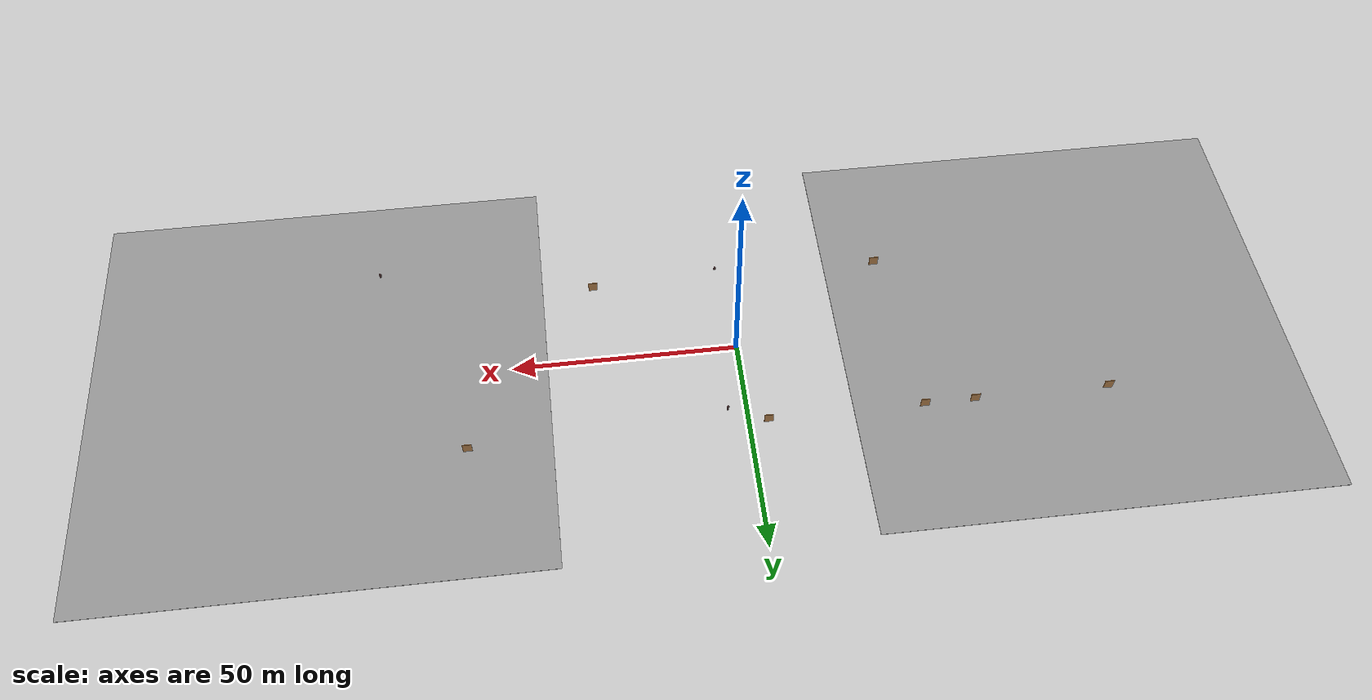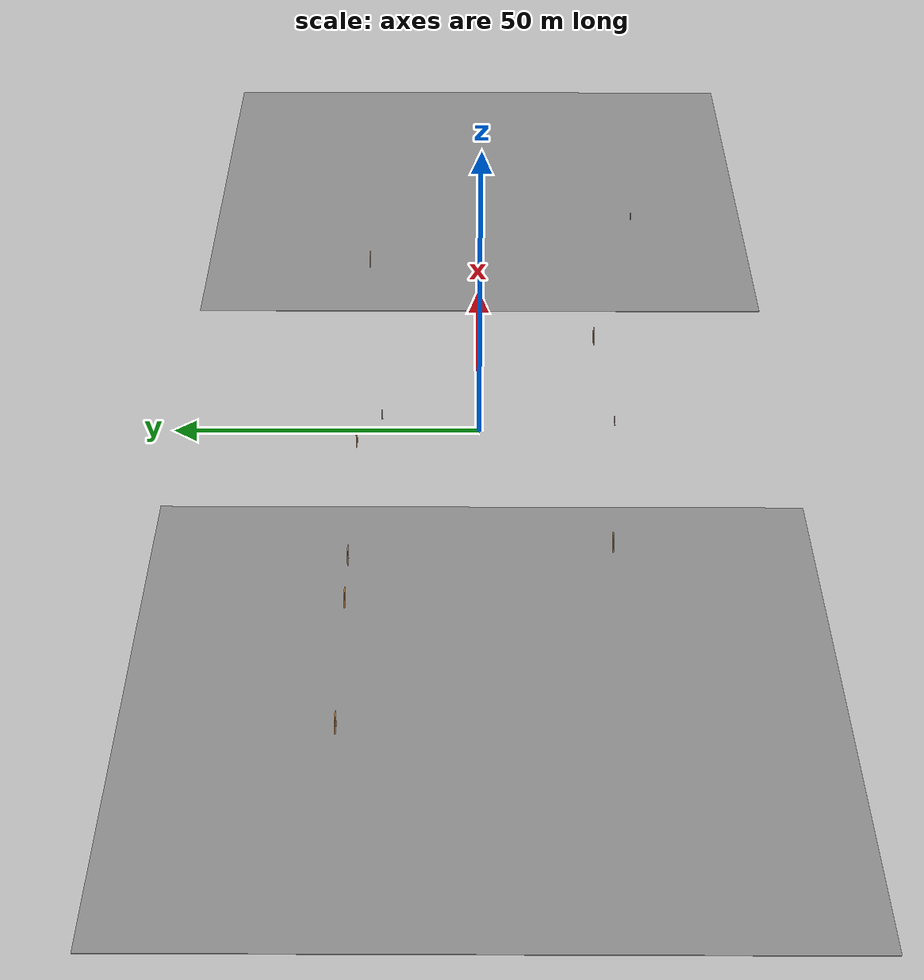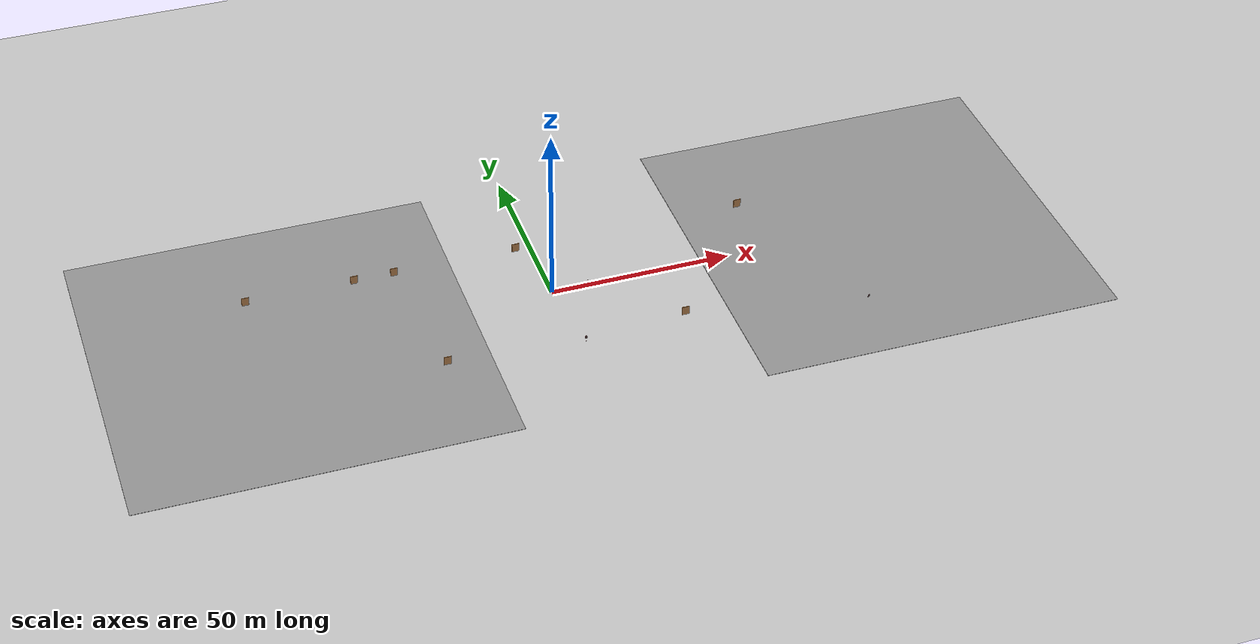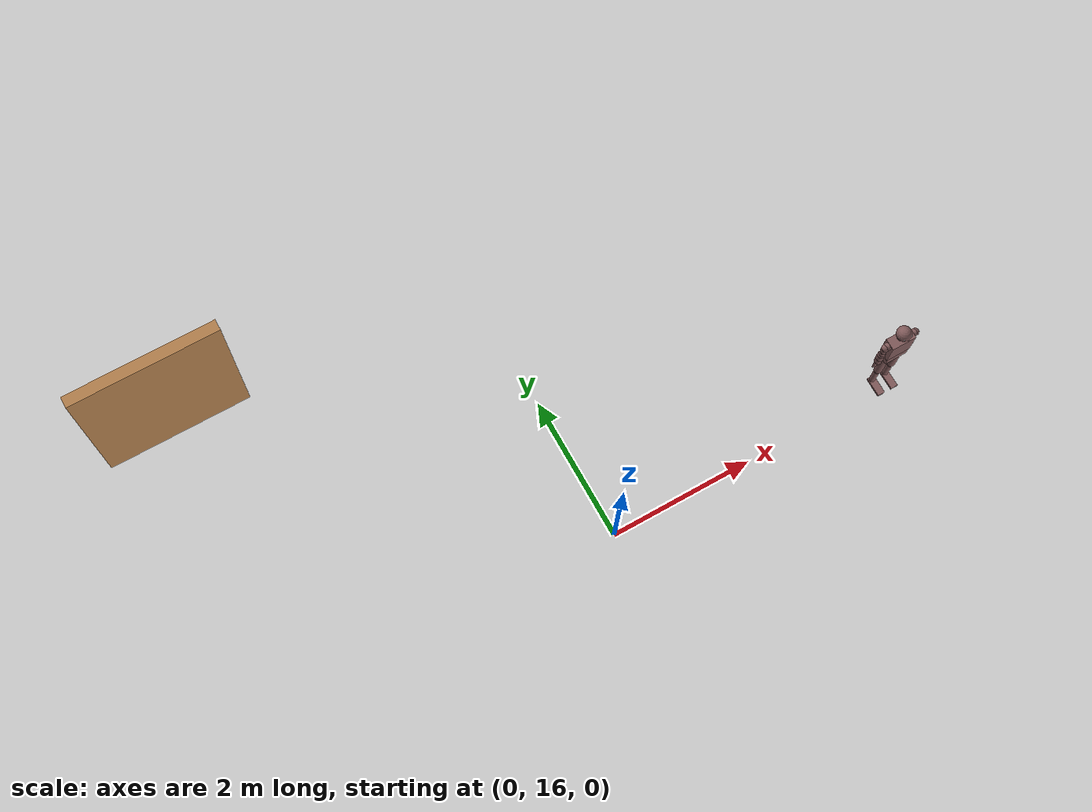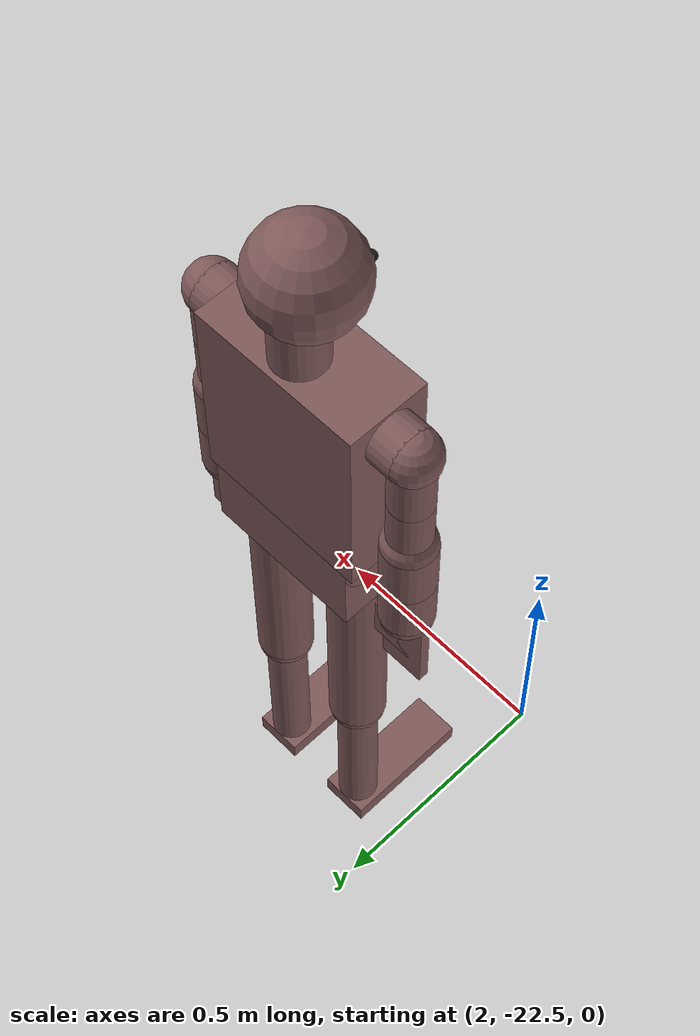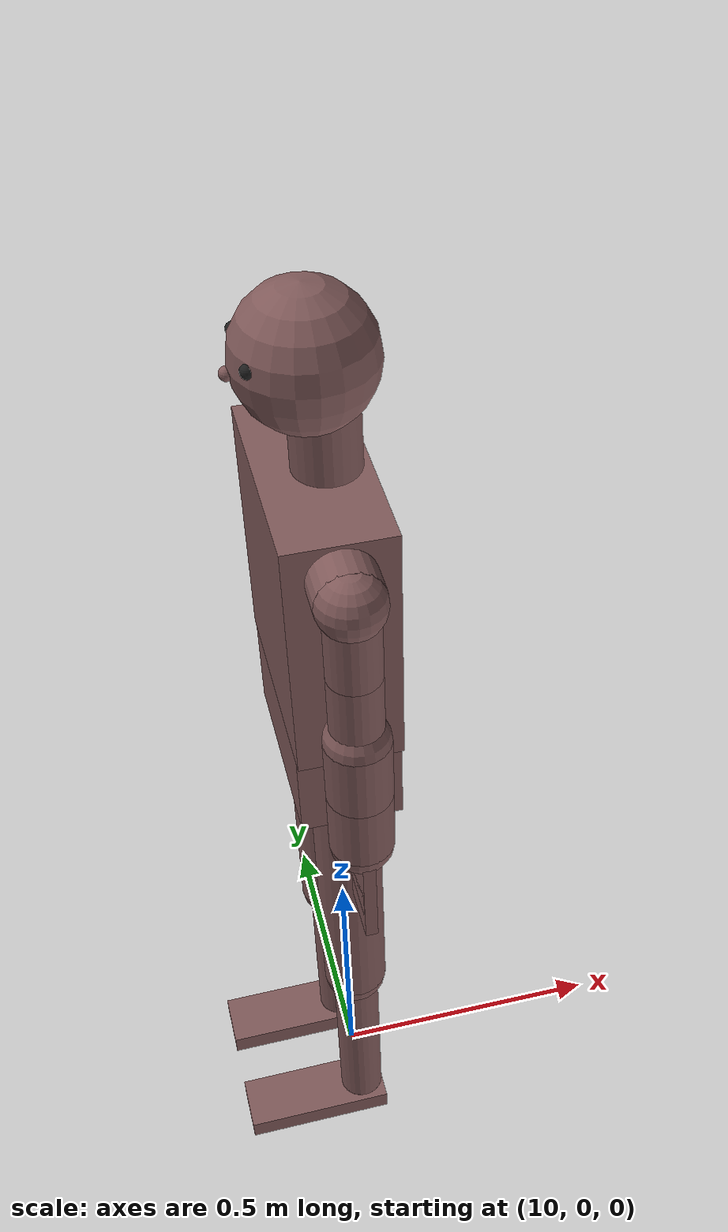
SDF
<sdf version="1.6">
 <world name="default">
  <light name="sun" type="directional">
   <pose>0 0 10 0 -0 0</pose>
   <diffuse>0.8 0.8 0.8 1</diffuse>
   <specular>0.2 0.2 0.2 1</specular>
   <attenuation>
    <range>1000</range>
    <constant>0.9</constant>
    <linear>0.01</linear>
    <quadratic>0.001</quadratic>
   </attenuation>
   <direction>-0.5 0.1 -0.9</direction>
  </light>
  <model name="ground_plane">
   <static>1</static>
   <link name="link">
    <collision name="collision">
     <geometry><plane><normal>0 0 1</normal><size>100 100</size></plane></geometry>
     <surface><friction><ode><mu>100</mu><mu2>50</mu2></ode></friction></surface>
    </collision>
    <visual name="visual">
     <cast_shadows>0</cast_shadows>
     <geometry><plane><normal>0 0 1</normal><size>100 100</size></plane></geometry>
     <material>
      <script><uri>file://media/materials/scripts/gazebo.material</uri><name>Gazebo/Grey</name></script>
     </material>
    </visual>
   </link>
  </model>
  <gravity>0 0 -9.8</gravity>
  <magnetic_field>6e-06 2.3e-05 -4.2e-05</magnetic_field>
  <atmosphere type="adiabatic"/>
  <physics name="default_physics" default="0" type="ode">
   <max_step_size>0.001</max_step_size>
   <real_time_factor>1</real_time_factor>
   <real_time_update_rate>1000</real_time_update_rate>
  </physics>
  <scene><ambient>0.4 0.4 0.4 1</ambient><background>0.7 0.7 0.7 1</background><shadows>1</shadows></scene>
  <spherical_coordinates>
   <surface_model>EARTH_WGS84</surface_model>
   <latitude_deg>0</latitude_deg>
   <longitude_deg>0</longitude_deg>
   <elevation>0</elevation>
   <heading_deg>0</heading_deg>
  </spherical_coordinates>
  <model name="ground_plane_0">
   <static>1</static>
   <link name="link">
    <collision name="collision">
     <geometry><plane><normal>0 0 1</normal><size>100 100</size></plane></geometry>
     <surface>
      <contact><collide_bitmask>65535</collide_bitmask></contact>
      <friction><ode><mu>100</mu><mu2>50</mu2></ode></friction>
     </surface>
    </collision>
    <visual name="visual">
     <cast_shadows>0</cast_shadows>
     <geometry><plane><normal>0 0 1</normal><size>100 100</size></plane></geometry>
     <material>
      <script><uri>file://media/materials/scripts/gazebo.material</uri><name>Gazebo/Grey</name></script>
     </material>
    </visual>
   </link>
   <pose>-72.9886 -0.147446 0 0 -0 0</pose>
  </model>
  <model name="ground_plane_1">
   <static>1</static>
   <link name="link">
    <collision name="collision">
     <geometry><plane><normal>0 0 1</normal><size>100 100</size></plane></geometry>
     <surface>
      <contact><collide_bitmask>65535</collide_bitmask></contact>
      <friction><ode><mu>100</mu><mu2>50</mu2></ode></friction>
     </surface>
    </collision>
    <visual name="visual">
     <cast_shadows>0</cast_shadows>
     <geometry><plane><normal>0 0 1</normal><size>100 100</size></plane></geometry>
     <material>
      <script><uri>file://media/materials/scripts/gazebo.material</uri><name>Gazebo/Grey</name></script>
     </material>
    </visual>
   </link>
   <pose>92.2083 -0.152614 0 0 -0 0</pose>
  </model>
  <model name="victim175_hot_moving">
   <static>1</static>
   <self_collide>1</self_collide>
   <link name="head">
    <pose>0 0 1.625 0 -0 0</pose>
    <visual name="visual">
     <geometry><sphere><radius>0.1</radius></sphere></geometry>
     <material>
      <emissive>0.5 0.35 0.35 1</emissive>
      <ambient>0.5 0.35 0.35 1</ambient>
      <diffuse>0.5 0.35 0.35 1</diffuse>
      <specular>0 0 0 0</specular>
     </material>
    </visual>
    <collision name="collision"><geometry><sphere><radius>0.1</radius></sphere></geometry></collision>
    <visual name="visual_nose">
     <pose>0 -0.1 -0.01 0 -0 0</pose>
     <geometry><sphere><radius>0.01</radius></sphere></geometry>
     <material>
      <emissive>0.5 0.35 0.35 1</emissive>
      <ambient>0.5 0.35 0.35 1</ambient>
      <diffuse>0.5 0.35 0.35 1</diffuse>
      <specular>0 0 0 0</specular>
     </material>
    </visual>
    <visual name="visual_rEye">
     <pose>-0.05 -0.08 0.02 0 -0 0</pose>
     <geometry><sphere><radius>0.01</radius></sphere></geometry>
     <material>
      <script><uri>file://media/materials/scripts/gazebo.material</uri><name>Gazebo/Black</name></script>
     </material>
    </visual>
    <visual name="visual_lEye">
     <pose>0.05 -0.08 0.02 0 -0 0</pose>
     <geometry><sphere><radius>0.01</radius></sphere></geometry>
     <material>
      <script><uri>file://media/materials/scripts/gazebo.material</uri><name>Gazebo/Black</name></script>
     </material>
    </visual>
    <self_collide>1</self_collide>
   </link>
   <link name="neck">
    <pose>0 0.02 1.49 0 -0 0</pose>
    <visual name="visual">
     <geometry><cylinder><radius>0.05</radius><length>0.15</length></cylinder></geometry>
     <material>
      <emissive>0.5 0.35 0.35 1</emissive>
      <ambient>0.5 0.35 0.35 1</ambient>
      <diffuse>0.5 0.35 0.35 1</diffuse>
      <specular>0 0 0 0</specular>
     </material>
    </visual>
    <collision name="collision">
     <geometry><cylinder><radius>0.05</radius><length>0.15</length></cylinder></geometry>
    </collision>
    <self_collide>1</self_collide>
   </link>
   <joint name="neck_head" type="revolute">
    <pose>0 0.02 -0.075 0 -0 0</pose>
    <child>head</child>
    <parent>neck</parent>
    <axis>
     <xyz>0 0 -1</xyz>
     <limit><lower>-1.7</lower><upper>1.7</upper></limit>
     <dynamics>
      <friction>0.01</friction>
      <spring_reference>0</spring_reference>
      <spring_stiffness>0</spring_stiffness>
     </dynamics>
     <use_parent_model_frame>0</use_parent_model_frame>
    </axis>
   </joint>
   <link name="body">
    <pose>0 0 1.255 0 -0 0</pose>
    <visual name="visual">
     <geometry><box><size>0.34 0.16 0.4</size></box></geometry>
     <material>
      <emissive>0.5 0.35 0.35 1</emissive>
      <ambient>0.5 0.35 0.35 1</ambient>
      <diffuse>0.5 0.35 0.35 1</diffuse>
      <specular>0 0 0 0</specular>
     </material>
    </visual>
    <collision name="collision"><geometry><box><size>0.34 0.16 0.4</size></box></geometry></collision>
    <self_collide>1</self_collide>
   </link>
   <joint name="body_neck" type="revolute">
    <pose>0 0.06 -0.075 0 -0 0</pose>
    <child>neck</child>
    <parent>body</parent>
    <axis>
     <xyz>1 0 0</xyz>
     <limit><lower>-0.2</lower><upper>1</upper></limit>
     <dynamics>
      <friction>0.01</friction>
      <spring_reference>0</spring_reference>
      <spring_stiffness>0</spring_stiffness>
     </dynamics>
     <use_parent_model_frame>0</use_parent_model_frame>
    </axis>
   </joint>
   <link name="waist">
    <pose>0 0 1.005 0 -0 0</pose>
    <visual name="visual">
     <pose>0 0 -0.025 0 -0 0</pose>
     <geometry><box><size>0.31 0.16 0.15</size></box></geometry>
     <material>
      <emissive>0.5 0.35 0.35 1</emissive>
      <ambient>0.5 0.35 0.35 1</ambient>
      <diffuse>0.5 0.35 0.35 1</diffuse>
      <specular>0 0 0 0</specular>
     </material>
    </visual>
    <collision name="collision"><geometry><box><size>0.31 0.16 0.1</size></box></geometry></collision>
    <visual name="visual2">
     <pose>0 0 0.05 3.14159 1.57079 3.14159</pose>
     <geometry><cylinder><radius>0.08</radius><length>0.31</length></cylinder></geometry>
     <material>
      <emissive>0.5 0.35 0.35 1</emissive>
      <ambient>0.5 0.35 0.35 1</ambient>
      <diffuse>0.5 0.35 0.35 1</diffuse>
      <specular>0 0 0 0</specular>
     </material>
    </visual>
    <collision name="collision2">
     <pose>0 0 0.05 3.14159 1.57079 3.14159</pose>
     <geometry><cylinder><radius>0.08</radius><length>0.31</length></cylinder></geometry>
    </collision>
    <self_collide>1</self_collide>
   </link>
   <joint name="body_waist" type="revolute">
    <pose>0 0 0.05 0 -0 0</pose>
    <child>waist</child>
    <parent>body</parent>
    <axis>
     <xyz>-1 0 0</xyz>
     <limit><lower>0</lower><upper>0</upper></limit>
     <dynamics>
      <friction>0.01</friction>
      <spring_reference>0</spring_reference>
      <spring_stiffness>0</spring_stiffness>
     </dynamics>
     <use_parent_model_frame>0</use_parent_model_frame>
    </axis>
   </joint>
   <link name="rHand">
    <pose>-0.22 0 0.84 0 -0 0</pose>
    <visual name="visual">
     <geometry><box><size>0.09 0.02 0.18</size></box></geometry>
     <material>
      <emissive>0.5 0.35 0.35 1</emissive>
      <ambient>0.5 0.35 0.35 1</ambient>
      <diffuse>0.5 0.35 0.35 1</diffuse>
      <specular>0 0 0 0</specular>
     </material>
    </visual>
    <collision name="collision"><geometry><box><size>0.09 0.02 0.18</size></box></geometry></collision>
    <visual name="visual2">
     <pose>0.02 0 0 0 -0 0</pose>
     <geometry><box><size>0.12 0.02 0.09</size></box></geometry>
     <material>
      <emissive>0.5 0.35 0.35 1</emissive>
      <ambient>0.5 0.35 0.35 1</ambient>
      <diffuse>0.5 0.35 0.35 1</diffuse>
      <specular>0 0 0 0</specular>
     </material>
    </visual>
    <collision name="collision2">
     <pose>0.02 0 0 0 -0 0</pose>
     <geometry><box><size>0.12 0.02 0.09</size></box></geometry>
    </collision>
    <self_collide>1</self_collide>
   </link>
   <link name="lHand">
    <pose>0.22 0 0.84 0 -0 0</pose>
    <visual name="visual">
     <geometry><box><size>0.09 0.02 0.18</size></box></geometry>
     <material>
      <emissive>0.5 0.35 0.35 1</emissive>
      <ambient>0.5 0.35 0.35 1</ambient>
      <diffuse>0.5 0.35 0.35 1</diffuse>
      <specular>0 0 0 0</specular>
     </material>
    </visual>
    <collision name="collision"><geometry><box><size>0.09 0.02 0.18</size></box></geometry></collision>
    <visual name="visual2">
     <pose>-0.02 0 0 0 -0 0</pose>
     <geometry><box><size>0.12 0.02 0.09</size></box></geometry>
     <material>
      <emissive>0.5 0.35 0.35 1</emissive>
      <ambient>0.5 0.35 0.35 1</ambient>
      <diffuse>0.5 0.35 0.35 1</diffuse>
      <specular>0 0 0 0</specular>
     </material>
    </visual>
    <collision name="collision2">
     <pose>-0.02 0 0 0 -0 0</pose>
     <geometry><box><size>0.12 0.02 0.09</size></box></geometry>
    </collision>
    <self_collide>1</self_collide>
   </link>
   <link name="rFoot">
    <pose>-0.1 -0.095 0.02 0 -0 0</pose>
    <visual name="visual">
     <geometry><box><size>0.1 0.27 0.04</size></box></geometry>
     <material>
      <emissive>0.5 0.35 0.35 1</emissive>
      <ambient>0.5 0.35 0.35 1</ambient>
      <diffuse>0.5 0.35 0.35 1</diffuse>
      <specular>0 0 0 0</specular>
     </material>
    </visual>
    <collision name="collision"><geometry><box><size>0.1 0.27 0.04</size></box></geometry></collision>
    <self_collide>1</self_collide>
   </link>
   <link name="lFoot">
    <pose>0.1 -0.095 0.02 0 -0 0</pose>
    <visual name="visual">
     <geometry><box><size>0.1 0.27 0.04</size></box></geometry>
     <material>
      <emissive>0.5 0.35 0.35 1</emissive>
      <ambient>0.5 0.35 0.35 1</ambient>
      <diffuse>0.5 0.35 0.35 1</diffuse>
      <specular>0 0 0 0</specular>
     </material>
    </visual>
    <collision name="collision"><geometry><box><size>0.1 0.27 0.04</size></box></geometry></collision>
    <self_collide>1</self_collide>
   </link>
   <link name="rLeg2">
    <pose>-0.1 0 0.23 0 -0 0</pose>
    <visual name="visual">
     <geometry><cylinder><radius>0.04</radius><length>0.38</length></cylinder></geometry>
     <material>
      <emissive>0.5 0.35 0.35 1</emissive>
      <ambient>0.5 0.35 0.35 1</ambient>
      <diffuse>0.5 0.35 0.35 1</diffuse>
      <specular>0 0 0 0</specular>
     </material>
    </visual>
    <collision name="collision">
     <geometry><cylinder><radius>0.04</radius><length>0.38</length></cylinder></geometry>
    </collision>
    <visual name="visual2">
     <pose>0 0 -0.19 0 -0 0</pose>
     <geometry><sphere><radius>0.04</radius></sphere></geometry>
     <material>
      <emissive>0.5 0.35 0.35 1</emissive>
      <ambient>0.5 0.35 0.35 1</ambient>
      <diffuse>0.5 0.35 0.35 1</diffuse>
      <specular>0 0 0 0</specular>
     </material>
    </visual>
    <collision name="collision2">
     <pose>0 0 -0.19 0 -0 0</pose>
     <geometry><sphere><radius>0.04</radius></sphere></geometry>
    </collision>
    <self_collide>1</self_collide>
   </link>
   <link name="lLeg2">
    <pose>0.1 0 0.23 0 -0 0</pose>
    <visual name="visual">
     <geometry><cylinder><radius>0.04</radius><length>0.38</length></cylinder></geometry>
     <material>
      <emissive>0.5 0.35 0.35 1</emissive>
      <ambient>0.5 0.35 0.35 1</ambient>
      <diffuse>0.5 0.35 0.35 1</diffuse>
      <specular>0 0 0 0</specular>
     </material>
    </visual>
    <collision name="collision">
     <geometry><cylinder><radius>0.04</radius><length>0.38</length></cylinder></geometry>
    </collision>
    <visual name="visual2">
     <pose>0 0 -0.19 0 -0 0</pose>
     <geometry><sphere><radius>0.04</radius></sphere></geometry>
     <material>
      <emissive>0.5 0.35 0.35 1</emissive>
      <ambient>0.5 0.35 0.35 1</ambient>
      <diffuse>0.5 0.35 0.35 1</diffuse>
      <specular>0 0 0 0</specular>
     </material>
    </visual>
    <collision name="collision2">
     <pose>0 0 -0.19 0 -0 0</pose>
     <geometry><sphere><radius>0.04</radius></sphere></geometry>
    </collision>
    <self_collide>1</self_collide>
   </link>
   <joint name="rLeg2_rFoot" type="revolute">
    <pose>0 0.095 0.02 0 -0 0</pose>
    <child>rFoot</child>
    <parent>rLeg2</parent>
    <axis>
     <xyz>1 0 0</xyz>
     <limit><lower>0</lower><upper>0</upper></limit>
     <dynamics>
      <friction>0.01</friction>
      <spring_reference>0</spring_reference>
      <spring_stiffness>0</spring_stiffness>
     </dynamics>
     <use_parent_model_frame>0</use_parent_model_frame>
    </axis>
   </joint>
   <joint name="lLeg2_lFoot" type="revolute">
    <pose>0 0.095 0.02 0 -0 0</pose>
    <child>lFoot</child>
    <parent>lLeg2</parent>
    <axis>
     <xyz>1 0 0</xyz>
     <limit><lower>0</lower><upper>0</upper></limit>
     <dynamics>
      <friction>0.01</friction>
      <spring_reference>0</spring_reference>
      <spring_stiffness>0</spring_stiffness>
     </dynamics>
     <use_parent_model_frame>0</use_parent_model_frame>
    </axis>
   </joint>
   <link name="rLeg1">
    <pose>-0.1 0 0.66 0 -0 0</pose>
    <visual name="visual">
     <geometry><cylinder><radius>0.055</radius><length>0.48</length></cylinder></geometry>
     <material>
      <emissive>0.5 0.35 0.35 1</emissive>
      <ambient>0.5 0.35 0.35 1</ambient>
      <diffuse>0.5 0.35 0.35 1</diffuse>
      <specular>0 0 0 0</specular>
     </material>
    </visual>
    <collision name="collision">
     <geometry><cylinder><radius>0.055</radius><length>0.48</length></cylinder></geometry>
    </collision>
    <visual name="visual2">
     <pose>0 0 -0.24 0 -0 0</pose>
     <geometry><sphere><radius>0.055</radius></sphere></geometry>
     <material>
      <emissive>0.5 0.35 0.35 1</emissive>
      <ambient>0.5 0.35 0.35 1</ambient>
      <diffuse>0.5 0.35 0.35 1</diffuse>
      <specular>0 0 0 0</specular>
     </material>
    </visual>
    <collision name="collision2">
     <pose>0 0 -0.24 0 -0 0</pose>
     <geometry><sphere><radius>0.055</radius></sphere></geometry>
    </collision>
    <visual name="visual3">
     <pose>0 0 0.24 0 -0 0</pose>
     <geometry><sphere><radius>0.055</radius></sphere></geometry>
     <material>
      <emissive>0.5 0.35 0.35 1</emissive>
      <ambient>0.5 0.35 0.35 1</ambient>
      <diffuse>0.5 0.35 0.35 1</diffuse>
      <specular>0 0 0 0</specular>
     </material>
    </visual>
    <collision name="collision3">
     <pose>0 0 0.24 0 -0 0</pose>
     <geometry><sphere><radius>0.055</radius></sphere></geometry>
    </collision>
    <self_collide>1</self_collide>
   </link>
   <link name="lLeg1">
    <pose>0.1 0 0.66 0 -0 0</pose>
    <visual name="visual">
     <geometry><cylinder><radius>0.055</radius><length>0.48</length></cylinder></geometry>
     <material>
      <emissive>0.5 0.35 0.35 1</emissive>
      <ambient>0.5 0.35 0.35 1</ambient>
      <diffuse>0.5 0.35 0.35 1</diffuse>
      <specular>0 0 0 0</specular>
     </material>
    </visual>
    <collision name="collision">
     <geometry><cylinder><radius>0.055</radius><length>0.48</length></cylinder></geometry>
    </collision>
    <visual name="visual2">
     <pose>0 0 -0.24 0 -0 0</pose>
     <geometry><sphere><radius>0.055</radius></sphere></geometry>
     <material>
      <emissive>0.5 0.35 0.35 1</emissive>
      <ambient>0.5 0.35 0.35 1</ambient>
      <diffuse>0.5 0.35 0.35 1</diffuse>
      <specular>0 0 0 0</specular>
     </material>
    </visual>
    <collision name="collision2">
     <pose>0 0 -0.24 0 -0 0</pose>
     <geometry><sphere><radius>0.055</radius></sphere></geometry>
    </collision>
    <visual name="visual3">
     <pose>0 0 0.24 0 -0 0</pose>
     <geometry><sphere><radius>0.055</radius></sphere></geometry>
     <material>
      <emissive>0.5 0.35 0.35 1</emissive>
      <ambient>0.5 0.35 0.35 1</ambient>
      <diffuse>0.5 0.35 0.35 1</diffuse>
      <specular>0 0 0 0</specular>
     </material>
    </visual>
    <collision name="collision3">
     <pose>0 0 0.24 0 -0 0</pose>
     <geometry><sphere><radius>0.055</radius></sphere></geometry>
    </collision>
    <self_collide>1</self_collide>
   </link>
   <joint name="rLeg1_rLeg2" type="revolute">
    <pose>0 0 0.19 0 -0 0</pose>
    <child>rLeg2</child>
    <parent>rLeg1</parent>
    <axis>
     <xyz>1 0 0</xyz>
     <limit><lower>0</lower><upper>0</upper></limit>
     <dynamics>
      <friction>0.01</friction>
      <spring_reference>0</spring_reference>
      <spring_stiffness>0</spring_stiffness>
     </dynamics>
     <use_parent_model_frame>0</use_parent_model_frame>
    </axis>
   </joint>
   <joint name="lLeg1_lLeg2" type="revolute">
    <pose>0 0 0.19 0 -0 0</pose>
    <child>lLeg2</child>
    <parent>lLeg1</parent>
    <axis>
     <xyz>1 0 0</xyz>
     <limit><lower>0</lower><upper>0</upper></limit>
     <dynamics>
      <friction>0.01</friction>
      <spring_reference>0</spring_reference>
      <spring_stiffness>0</spring_stiffness>
     </dynamics>
     <use_parent_model_frame>0</use_parent_model_frame>
    </axis>
   </joint>
   <link name="rButt">
    <pose>-0.1 0 0.9275 0 -0 0</pose>
    <visual name="visual">
     <geometry><cylinder><radius>0.055</radius><length>0.055</length></cylinder></geometry>
     <material>
      <emissive>0.5 0.35 0.35 1</emissive>
      <ambient>0.5 0.35 0.35 1</ambient>
      <diffuse>0.5 0.35 0.35 1</diffuse>
      <specular>0 0 0 0</specular>
     </material>
    </visual>
    <collision name="collision">
     <geometry><cylinder><radius>0.055</radius><length>0.055</length></cylinder></geometry>
    </collision>
    <self_collide>1</self_collide>
   </link>
   <link name="lButt">
    <pose>0.1 0 0.9275 0 -0 0</pose>
    <visual name="visual">
     <geometry><cylinder><radius>0.055</radius><length>0.055</length></cylinder></geometry>
     <material>
      <emissive>0.5 0.35 0.35 1</emissive>
      <ambient>0.5 0.35 0.35 1</ambient>
      <diffuse>0.5 0.35 0.35 1</diffuse>
      <specular>0 0 0 0</specular>
     </material>
    </visual>
    <collision name="collision">
     <geometry><cylinder><radius>0.055</radius><length>0.055</length></cylinder></geometry>
    </collision>
    <self_collide>1</self_collide>
   </link>
   <joint name="rButt_rLeg1" type="revolute">
    <pose>0 0 0.24 0 -0 0</pose>
    <child>rLeg1</child>
    <parent>rButt</parent>
    <axis>
     <xyz>1 0 0</xyz>
     <limit><lower>0</lower><upper>0</upper></limit>
     <dynamics>
      <friction>0.01</friction>
      <spring_reference>0</spring_reference>
      <spring_stiffness>0</spring_stiffness>
     </dynamics>
     <use_parent_model_frame>0</use_parent_model_frame>
    </axis>
   </joint>
   <joint name="lButt_lLeg1" type="revolute">
    <pose>0 0 0.24 0 -0 0</pose>
    <child>lLeg1</child>
    <parent>lButt</parent>
    <axis>
     <xyz>1 0 0</xyz>
     <limit><lower>0</lower><upper>0</upper></limit>
     <dynamics>
      <friction>0.01</friction>
      <spring_reference>0</spring_reference>
      <spring_stiffness>0</spring_stiffness>
     </dynamics>
     <use_parent_model_frame>0</use_parent_model_frame>
    </axis>
   </joint>
   <joint name="waist_rButt" type="revolute">
    <child>rButt</child>
    <parent>waist</parent>
    <axis>
     <xyz>0 0 -1</xyz>
     <limit><lower>-1</lower><upper>1</upper></limit>
     <dynamics>
      <friction>0.01</friction>
      <spring_reference>0</spring_reference>
      <spring_stiffness>0</spring_stiffness>
     </dynamics>
     <use_parent_model_frame>0</use_parent_model_frame>
    </axis>
   </joint>
   <joint name="waist_lButt" type="revolute">
    <child>lButt</child>
    <parent>waist</parent>
    <axis>
     <xyz>0 0 1</xyz>
     <limit><lower>-1</lower><upper>1</upper></limit>
     <dynamics>
      <friction>0.01</friction>
      <spring_reference>0</spring_reference>
      <spring_stiffness>0</spring_stiffness>
     </dynamics>
     <use_parent_model_frame>0</use_parent_model_frame>
    </axis>
   </joint>
   <link name="rShoulder">
    <pose>-0.195 0 1.4 0 -0 0</pose>
    <visual name="visual">
     <pose>0 0 0 3.14159 1.57079 3.14159</pose>
     <geometry><cylinder><radius>0.05</radius><length>0.05</length></cylinder></geometry>
     <material>
      <emissive>0.5 0.35 0.35 1</emissive>
      <ambient>0.5 0.35 0.35 1</ambient>
      <diffuse>0.5 0.35 0.35 1</diffuse>
      <specular>0 0 0 0</specular>
     </material>
    </visual>
    <collision name="collision">
     <pose>0 0 0 3.14159 1.57079 3.14159</pose>
     <geometry><cylinder><radius>0.05</radius><length>0.05</length></cylinder></geometry>
    </collision>
    <self_collide>1</self_collide>
   </link>
   <link name="lShoulder">
    <pose>0.195 0 1.4 0 -0 0</pose>
    <visual name="visual">
     <pose>0 0 0 3.14159 1.57079 3.14159</pose>
     <geometry><cylinder><radius>0.05</radius><length>0.05</length></cylinder></geometry>
     <material>
      <emissive>0.5 0.35 0.35 1</emissive>
      <ambient>0.5 0.35 0.35 1</ambient>
      <diffuse>0.5 0.35 0.35 1</diffuse>
      <specular>0 0 0 0</specular>
     </material>
    </visual>
    <collision name="collision">
     <pose>0 0 0 3.14159 1.57079 3.14159</pose>
     <geometry><cylinder><radius>0.05</radius><length>0.05</length></cylinder></geometry>
    </collision>
    <self_collide>1</self_collide>
   </link>
   <joint name="body_rShoulder" type="revolute">
    <child>rShoulder</child>
    <parent>body</parent>
    <axis>
     <xyz>-1 0 0</xyz>
     <limit><lower>-1.5708</lower><upper>3.2</upper></limit>
     <dynamics>
      <friction>0.01</friction>
      <spring_reference>0</spring_reference>
      <spring_stiffness>0</spring_stiffness>
     </dynamics>
     <use_parent_model_frame>0</use_parent_model_frame>
    </axis>
   </joint>
   <joint name="body_lShoulder" type="revolute">
    <child>lShoulder</child>
    <parent>body</parent>
    <axis>
     <xyz>1 0 0</xyz>
     <limit><lower>-1.5708</lower><upper>3.2</upper></limit>
     <dynamics>
      <friction>0.01</friction>
      <spring_reference>0</spring_reference>
      <spring_stiffness>0</spring_stiffness>
     </dynamics>
     <use_parent_model_frame>0</use_parent_model_frame>
    </axis>
   </joint>
   <link name="rArm1U">
    <pose>-0.22 0 1.3375 0 -0 0</pose>
    <visual name="visual">
     <geometry><cylinder><radius>0.04</radius><length>0.125</length></cylinder></geometry>
     <material>
      <emissive>0.5 0.35 0.35 1</emissive>
      <ambient>0.5 0.35 0.35 1</ambient>
      <diffuse>0.5 0.35 0.35 1</diffuse>
      <specular>0 0 0 0</specular>
     </material>
    </visual>
    <collision name="collision">
     <geometry><cylinder><radius>0.04</radius><length>0.125</length></cylinder></geometry>
    </collision>
    <visual name="visual2">
     <pose>0 0 0.0625 0 -0 0</pose>
     <geometry><sphere><radius>0.05</radius></sphere></geometry>
     <material>
      <emissive>0.5 0.35 0.35 1</emissive>
      <ambient>0.5 0.35 0.35 1</ambient>
      <diffuse>0.5 0.35 0.35 1</diffuse>
      <specular>0 0 0 0</specular>
     </material>
    </visual>
    <collision name="collision2">
     <pose>0 0 0.0625 0 -0 0</pose>
     <geometry><sphere><radius>0.05</radius></sphere></geometry>
    </collision>
    <self_collide>1</self_collide>
   </link>
   <link name="rArm1L">
    <pose>-0.22 0 1.2125 0 -0 0</pose>
    <visual name="visual">
     <geometry><cylinder><radius>0.04</radius><length>0.125</length></cylinder></geometry>
     <material>
      <emissive>0.5 0.35 0.35 1</emissive>
      <ambient>0.5 0.35 0.35 1</ambient>
      <diffuse>0.5 0.35 0.35 1</diffuse>
      <specular>0 0 0 0</specular>
     </material>
    </visual>
    <collision name="collision">
     <geometry><cylinder><radius>0.04</radius><length>0.125</length></cylinder></geometry>
    </collision>
    <visual name="visual2">
     <pose>0 0 -0.0625 0 -0 0</pose>
     <geometry><sphere><radius>0.05</radius></sphere></geometry>
     <material>
      <emissive>0.5 0.35 0.35 1</emissive>
      <ambient>0.5 0.35 0.35 1</ambient>
      <diffuse>0.5 0.35 0.35 1</diffuse>
      <specular>0 0 0 0</specular>
     </material>
    </visual>
    <collision name="collision2">
     <pose>0 0 -0.0625 0 -0 0</pose>
     <geometry><sphere><radius>0.05</radius></sphere></geometry>
    </collision>
    <self_collide>1</self_collide>
   </link>
   <joint name="rArm1U_rArm1L" type="revolute">
    <pose>0 0 0.0625 0 -0 0</pose>
    <child>rArm1L</child>
    <parent>rArm1U</parent>
    <axis>
     <xyz>0 0 -1</xyz>
     <limit><lower>-1.5708</lower><upper>1.5708</upper></limit>
     <dynamics>
      <friction>0.01</friction>
      <spring_reference>0</spring_reference>
      <spring_stiffness>0</spring_stiffness>
     </dynamics>
     <use_parent_model_frame>0</use_parent_model_frame>
    </axis>
   </joint>
   <link name="lArm1U">
    <pose>0.22 0 1.3375 0 -0 0</pose>
    <visual name="visual">
     <geometry><cylinder><radius>0.04</radius><length>0.125</length></cylinder></geometry>
     <material>
      <emissive>0.5 0.35 0.35 1</emissive>
      <ambient>0.5 0.35 0.35 1</ambient>
      <diffuse>0.5 0.35 0.35 1</diffuse>
      <specular>0 0 0 0</specular>
     </material>
    </visual>
    <collision name="collision">
     <geometry><cylinder><radius>0.04</radius><length>0.125</length></cylinder></geometry>
    </collision>
    <visual name="visual2">
     <pose>0 0 0.0625 0 -0 0</pose>
     <geometry><sphere><radius>0.05</radius></sphere></geometry>
     <material>
      <emissive>0.5 0.35 0.35 1</emissive>
      <ambient>0.5 0.35 0.35 1</ambient>
      <diffuse>0.5 0.35 0.35 1</diffuse>
      <specular>0 0 0 0</specular>
     </material>
    </visual>
    <collision name="collision2">
     <pose>0 0 0.0625 0 -0 0</pose>
     <geometry><sphere><radius>0.05</radius></sphere></geometry>
    </collision>
    <self_collide>1</self_collide>
   </link>
   <link name="lArm1L">
    <pose>0.22 0 1.2125 0 -0 0</pose>
    <visual name="visual">
     <geometry><cylinder><radius>0.04</radius><length>0.125</length></cylinder></geometry>
     <material>
      <emissive>0.5 0.35 0.35 1</emissive>
      <ambient>0.5 0.35 0.35 1</ambient>
      <diffuse>0.5 0.35 0.35 1</diffuse>
      <specular>0 0 0 0</specular>
     </material>
    </visual>
    <collision name="collision">
     <geometry><cylinder><radius>0.04</radius><length>0.125</length></cylinder></geometry>
    </collision>
    <visual name="visual2">
     <pose>0 0 -0.0625 0 -0 0</pose>
     <geometry><sphere><radius>0.05</radius></sphere></geometry>
     <material>
      <emissive>0.5 0.35 0.35 1</emissive>
      <ambient>0.5 0.35 0.35 1</ambient>
      <diffuse>0.5 0.35 0.35 1</diffuse>
      <specular>0 0 0 0</specular>
     </material>
    </visual>
    <collision name="collision2">
     <pose>0 0 -0.0625 0 -0 0</pose>
     <geometry><sphere><radius>0.05</radius></sphere></geometry>
    </collision>
    <self_collide>1</self_collide>
   </link>
   <joint name="lArm1U_lArm1L" type="revolute">
    <pose>0 0 0.0625 0 -0 0</pose>
    <child>lArm1L</child>
    <parent>lArm1U</parent>
    <axis>
     <xyz>0 0 1</xyz>
     <limit><lower>-1.5708</lower><upper>1.5708</upper></limit>
     <dynamics>
      <friction>0.01</friction>
      <spring_reference>0</spring_reference>
      <spring_stiffness>0</spring_stiffness>
     </dynamics>
     <use_parent_model_frame>0</use_parent_model_frame>
    </axis>
   </joint>
   <joint name="rShoulder_rArm1" type="revolute">
    <pose>0 0 0.0625 0 -0 0</pose>
    <child>rArm1U</child>
    <parent>rShoulder</parent>
    <axis>
     <xyz>0 -1 0</xyz>
     <limit><lower>-1.5708</lower><upper>3.2</upper></limit>
     <dynamics>
      <friction>0.01</friction>
      <spring_reference>0</spring_reference>
      <spring_stiffness>0</spring_stiffness>
     </dynamics>
     <use_parent_model_frame>0</use_parent_model_frame>
    </axis>
   </joint>
   <joint name="lShoulder_lArm1" type="revolute">
    <pose>0 0 0.0625 0 -0 0</pose>
    <child>lArm1U</child>
    <parent>lShoulder</parent>
    <axis>
     <xyz>0 1 0</xyz>
     <limit><lower>-1.5708</lower><upper>3.2</upper></limit>
     <dynamics>
      <friction>0.01</friction>
      <spring_reference>0</spring_reference>
      <spring_stiffness>0</spring_stiffness>
     </dynamics>
     <use_parent_model_frame>0</use_parent_model_frame>
    </axis>
   </joint>
   <link name="rArm2U">
    <pose>-0.22 0 1.095 0 -0 0</pose>
    <visual name="visual">
     <geometry><cylinder><radius>0.05</radius><length>0.11</length></cylinder></geometry>
     <material>
      <emissive>0.5 0.35 0.35 1</emissive>
      <ambient>0.5 0.35 0.35 1</ambient>
      <diffuse>0.5 0.35 0.35 1</diffuse>
      <specular>0 0 0 0</specular>
     </material>
    </visual>
    <collision name="collision">
     <geometry><cylinder><radius>0.05</radius><length>0.11</length></cylinder></geometry>
    </collision>
    <self_collide>1</self_collide>
   </link>
   <link name="rArm2L">
    <pose>-0.22 0 0.985 0 -0 0</pose>
    <visual name="visual">
     <geometry><cylinder><radius>0.05</radius><length>0.11</length></cylinder></geometry>
     <material>
      <emissive>0.5 0.35 0.35 1</emissive>
      <ambient>0.5 0.35 0.35 1</ambient>
      <diffuse>0.5 0.35 0.35 1</diffuse>
      <specular>0 0 0 0</specular>
     </material>
    </visual>
    <collision name="collision">
     <geometry><cylinder><radius>0.05</radius><length>0.11</length></cylinder></geometry>
    </collision>
    <visual name="visual2">
     <pose>0 0 -0.055 0 -0 0</pose>
     <geometry><sphere><radius>0.05</radius></sphere></geometry>
     <material>
      <emissive>0.5 0.35 0.35 1</emissive>
      <ambient>0.5 0.35 0.35 1</ambient>
      <diffuse>0.5 0.35 0.35 1</diffuse>
      <specular>0 0 0 0</specular>
     </material>
    </visual>
    <collision name="collision2">
     <pose>0 0 -0.055 0 -0 0</pose>
     <geometry><sphere><radius>0.05</radius></sphere></geometry>
    </collision>
    <self_collide>1</self_collide>
   </link>
   <joint name="rArm2U_rArm2L" type="revolute">
    <pose>0 0 0.055 0 -0 0</pose>
    <child>rArm2L</child>
    <parent>rArm2U</parent>
    <axis>
     <xyz>0 0 -1</xyz>
     <limit><lower>-1.5708</lower><upper>1.5708</upper></limit>
     <dynamics>
      <friction>0.01</friction>
      <spring_reference>0</spring_reference>
      <spring_stiffness>0</spring_stiffness>
     </dynamics>
     <use_parent_model_frame>0</use_parent_model_frame>
    </axis>
   </joint>
   <link name="lArm2U">
    <pose>0.22 0 1.095 0 -0 0</pose>
    <visual name="visual">
     <geometry><cylinder><radius>0.05</radius><length>0.11</length></cylinder></geometry>
     <material>
      <emissive>0.5 0.35 0.35 1</emissive>
      <ambient>0.5 0.35 0.35 1</ambient>
      <diffuse>0.5 0.35 0.35 1</diffuse>
      <specular>0 0 0 0</specular>
     </material>
    </visual>
    <collision name="collision">
     <geometry><cylinder><radius>0.05</radius><length>0.11</length></cylinder></geometry>
    </collision>
    <self_collide>1</self_collide>
   </link>
   <link name="lArm2L">
    <pose>0.22 0 0.985 0 -0 0</pose>
    <visual name="visual">
     <geometry><cylinder><radius>0.05</radius><length>0.11</length></cylinder></geometry>
     <material>
      <emissive>0.5 0.35 0.35 1</emissive>
      <ambient>0.5 0.35 0.35 1</ambient>
      <diffuse>0.5 0.35 0.35 1</diffuse>
      <specular>0 0 0 0</specular>
     </material>
    </visual>
    <collision name="collision">
     <geometry><cylinder><radius>0.05</radius><length>0.11</length></cylinder></geometry>
    </collision>
    <visual name="visual2">
     <pose>0 0 -0.055 0 -0 0</pose>
     <geometry><sphere><radius>0.05</radius></sphere></geometry>
     <material>
      <emissive>0.5 0.35 0.35 1</emissive>
      <ambient>0.5 0.35 0.35 1</ambient>
      <diffuse>0.5 0.35 0.35 1</diffuse>
      <specular>0 0 0 0</specular>
     </material>
    </visual>
    <collision name="collision2">
     <pose>0 0 -0.055 0 -0 0</pose>
     <geometry><sphere><radius>0.05</radius></sphere></geometry>
    </collision>
    <self_collide>1</self_collide>
   </link>
   <joint name="lArm2U_lArm2L" type="revolute">
    <pose>0 0 0.055 0 -0 0</pose>
    <child>lArm2L</child>
    <parent>lArm2U</parent>
    <axis>
     <xyz>0 0 1</xyz>
     <limit><lower>-1.5708</lower><upper>1.5708</upper></limit>
     <dynamics>
      <friction>0.01</friction>
      <spring_reference>0</spring_reference>
      <spring_stiffness>0</spring_stiffness>
     </dynamics>
     <use_parent_model_frame>0</use_parent_model_frame>
    </axis>
   </joint>
   <joint name="rArm1_rArm2" type="revolute">
    <pose>0 0 0.055 0 -0 0</pose>
    <child>rArm2U</child>
    <parent>rArm1L</parent>
    <axis>
     <xyz>-1 0 0</xyz>
     <limit><lower>0</lower><upper>2.8</upper></limit>
     <dynamics>
      <friction>0.01</friction>
      <spring_reference>0</spring_reference>
      <spring_stiffness>0</spring_stiffness>
     </dynamics>
     <use_parent_model_frame>0</use_parent_model_frame>
    </axis>
   </joint>
   <joint name="lArm1_lArm2" type="revolute">
    <pose>0 0 0.055 0 -0 0</pose>
    <child>lArm2U</child>
    <parent>lArm1L</parent>
    <axis>
     <xyz>-1 0 0</xyz>
     <limit><lower>0</lower><upper>2.8</upper></limit>
     <dynamics>
      <friction>0.01</friction>
      <spring_reference>0</spring_reference>
      <spring_stiffness>0</spring_stiffness>
     </dynamics>
     <use_parent_model_frame>0</use_parent_model_frame>
    </axis>
   </joint>
   <joint name="rArm2_rHand" type="revolute">
    <pose>0 0 0.09 0 -0 0</pose>
    <child>rHand</child>
    <parent>rArm2L</parent>
    <axis>
     <xyz>-1 0 0</xyz>
     <limit><lower>-1.57</lower><upper>1.4</upper></limit>
     <dynamics>
      <friction>0.01</friction>
      <spring_reference>0</spring_reference>
      <spring_stiffness>0</spring_stiffness>
     </dynamics>
     <use_parent_model_frame>0</use_parent_model_frame>
    </axis>
   </joint>
   <joint name="lArm2_lHand" type="revolute">
    <pose>0 0 0.09 0 -0 0</pose>
    <child>lHand</child>
    <parent>lArm2L</parent>
    <axis>
     <xyz>-1 0 0</xyz>
     <limit><lower>-1.57</lower><upper>1.4</upper></limit>
     <dynamics>
      <friction>0.01</friction>
      <spring_reference>0</spring_reference>
      <spring_stiffness>0</spring_stiffness>
     </dynamics>
     <use_parent_model_frame>0</use_parent_model_frame>
    </axis>
   </joint>
   <joint name="world_rFoot" type="revolute">
    <child>rFoot</child>
    <parent>world</parent>
    <axis>
     <xyz>0 0 1</xyz>
     <limit><lower>0</lower><upper>0</upper></limit>
     <use_parent_model_frame>0</use_parent_model_frame>
     <dynamics><spring_reference>0</spring_reference><spring_stiffness>0</spring_stiffness></dynamics>
    </axis>
   </joint>
   <joint name="world_lFoot" type="revolute">
    <child>lFoot</child>
    <parent>world</parent>
    <axis>
     <xyz>0 0 1</xyz>
     <limit><lower>0</lower><upper>0</upper></limit>
     <use_parent_model_frame>0</use_parent_model_frame>
     <dynamics><spring_reference>0</spring_reference><spring_stiffness>0</spring_stiffness></dynamics>
    </axis>
   </joint>
   <pose>2.21827 -22.126 0 0 -0 0</pose>
  </model>
  <model name="victim175_hot_moving_clone_clone_0">
   <static>1</static>
   <self_collide>1</self_collide>
   <link name="head">
    <pose>0 0 1.625 0 -0 0</pose>
    <visual name="visual">
     <geometry><sphere><radius>0.1</radius></sphere></geometry>
     <material>
      <emissive>0.5 0.35 0.35 1</emissive>
      <ambient>0.5 0.35 0.35 1</ambient>
      <diffuse>0.5 0.35 0.35 1</diffuse>
      <specular>0 0 0 0</specular>
     </material>
    </visual>
    <collision name="collision"><geometry><sphere><radius>0.1</radius></sphere></geometry></collision>
    <visual name="visual_nose">
     <pose>0 -0.1 -0.01 0 -0 0</pose>
     <geometry><sphere><radius>0.01</radius></sphere></geometry>
     <material>
      <emissive>0.5 0.35 0.35 1</emissive>
      <ambient>0.5 0.35 0.35 1</ambient>
      <diffuse>0.5 0.35 0.35 1</diffuse>
      <specular>0 0 0 0</specular>
     </material>
    </visual>
    <visual name="visual_rEye">
     <pose>-0.05 -0.08 0.02 0 -0 0</pose>
     <geometry><sphere><radius>0.01</radius></sphere></geometry>
     <material>
      <script><uri>file://media/materials/scripts/gazebo.material</uri><name>Gazebo/Black</name></script>
     </material>
    </visual>
    <visual name="visual_lEye">
     <pose>0.05 -0.08 0.02 0 -0 0</pose>
     <geometry><sphere><radius>0.01</radius></sphere></geometry>
     <material>
      <script><uri>file://media/materials/scripts/gazebo.material</uri><name>Gazebo/Black</name></script>
     </material>
    </visual>
    <self_collide>1</self_collide>
   </link>
   <link name="neck">
    <pose>0 0.02 1.49 0 -0 0</pose>
    <visual name="visual">
     <geometry><cylinder><radius>0.05</radius><length>0.15</length></cylinder></geometry>
     <material>
      <emissive>0.5 0.35 0.35 1</emissive>
      <ambient>0.5 0.35 0.35 1</ambient>
      <diffuse>0.5 0.35 0.35 1</diffuse>
      <specular>0 0 0 0</specular>
     </material>
    </visual>
    <collision name="collision">
     <geometry><cylinder><radius>0.05</radius><length>0.15</length></cylinder></geometry>
    </collision>
    <self_collide>1</self_collide>
   </link>
   <joint name="neck_head" type="revolute">
    <pose>0 0.02 -0.075 0 -0 0</pose>
    <child>head</child>
    <parent>neck</parent>
    <axis>
     <xyz>0 0 -1</xyz>
     <limit><lower>-1.7</lower><upper>1.7</upper></limit>
     <dynamics>
      <friction>0.01</friction>
      <spring_reference>0</spring_reference>
      <spring_stiffness>0</spring_stiffness>
     </dynamics>
     <use_parent_model_frame>0</use_parent_model_frame>
    </axis>
   </joint>
   <link name="body">
    <pose>0 0 1.255 0 -0 0</pose>
    <visual name="visual">
     <geometry><box><size>0.34 0.16 0.4</size></box></geometry>
     <material>
      <emissive>0.5 0.35 0.35 1</emissive>
      <ambient>0.5 0.35 0.35 1</ambient>
      <diffuse>0.5 0.35 0.35 1</diffuse>
      <specular>0 0 0 0</specular>
     </material>
    </visual>
    <collision name="collision"><geometry><box><size>0.34 0.16 0.4</size></box></geometry></collision>
    <self_collide>1</self_collide>
   </link>
   <joint name="body_neck" type="revolute">
    <pose>0 0.06 -0.075 0 -0 0</pose>
    <child>neck</child>
    <parent>body</parent>
    <axis>
     <xyz>1 0 0</xyz>
     <limit><lower>-0.2</lower><upper>1</upper></limit>
     <dynamics>
      <friction>0.01</friction>
      <spring_reference>0</spring_reference>
      <spring_stiffness>0</spring_stiffness>
     </dynamics>
     <use_parent_model_frame>0</use_parent_model_frame>
    </axis>
   </joint>
   <link name="waist">
    <pose>0 0 1.005 0 -0 0</pose>
    <visual name="visual">
     <pose>0 0 -0.025 0 -0 0</pose>
     <geometry><box><size>0.31 0.16 0.15</size></box></geometry>
     <material>
      <emissive>0.5 0.35 0.35 1</emissive>
      <ambient>0.5 0.35 0.35 1</ambient>
      <diffuse>0.5 0.35 0.35 1</diffuse>
      <specular>0 0 0 0</specular>
     </material>
    </visual>
    <collision name="collision"><geometry><box><size>0.31 0.16 0.1</size></box></geometry></collision>
    <visual name="visual2">
     <pose>0 0 0.05 3.14159 1.57079 3.14159</pose>
     <geometry><cylinder><radius>0.08</radius><length>0.31</length></cylinder></geometry>
     <material>
      <emissive>0.5 0.35 0.35 1</emissive>
      <ambient>0.5 0.35 0.35 1</ambient>
      <diffuse>0.5 0.35 0.35 1</diffuse>
      <specular>0 0 0 0</specular>
     </material>
    </visual>
    <collision name="collision2">
     <pose>0 0 0.05 3.14159 1.57079 3.14159</pose>
     <geometry><cylinder><radius>0.08</radius><length>0.31</length></cylinder></geometry>
    </collision>
    <self_collide>1</self_collide>
   </link>
   <joint name="body_waist" type="revolute">
    <pose>0 0 0.05 0 -0 0</pose>
    <child>waist</child>
    <parent>body</parent>
    <axis>
     <xyz>-1 0 0</xyz>
     <limit><lower>0</lower><upper>0</upper></limit>
     <dynamics>
      <friction>0.01</friction>
      <spring_reference>0</spring_reference>
      <spring_stiffness>0</spring_stiffness>
     </dynamics>
     <use_parent_model_frame>0</use_parent_model_frame>
    </axis>
   </joint>
   <link name="rHand">
    <pose>-0.22 0 0.84 0 -0 0</pose>
    <visual name="visual">
     <geometry><box><size>0.09 0.02 0.18</size></box></geometry>
     <material>
      <emissive>0.5 0.35 0.35 1</emissive>
      <ambient>0.5 0.35 0.35 1</ambient>
      <diffuse>0.5 0.35 0.35 1</diffuse>
      <specular>0 0 0 0</specular>
     </material>
    </visual>
    <collision name="collision"><geometry><box><size>0.09 0.02 0.18</size></box></geometry></collision>
    <visual name="visual2">
     <pose>0.02 0 0 0 -0 0</pose>
     <geometry><box><size>0.12 0.02 0.09</size></box></geometry>
     <material>
      <emissive>0.5 0.35 0.35 1</emissive>
      <ambient>0.5 0.35 0.35 1</ambient>
      <diffuse>0.5 0.35 0.35 1</diffuse>
      <specular>0 0 0 0</specular>
     </material>
    </visual>
    <collision name="collision2">
     <pose>0.02 0 0 0 -0 0</pose>
     <geometry><box><size>0.12 0.02 0.09</size></box></geometry>
    </collision>
    <self_collide>1</self_collide>
   </link>
   <link name="lHand">
    <pose>0.22 0 0.84 0 -0 0</pose>
    <visual name="visual">
     <geometry><box><size>0.09 0.02 0.18</size></box></geometry>
     <material>
      <emissive>0.5 0.35 0.35 1</emissive>
      <ambient>0.5 0.35 0.35 1</ambient>
      <diffuse>0.5 0.35 0.35 1</diffuse>
      <specular>0 0 0 0</specular>
     </material>
    </visual>
    <collision name="collision"><geometry><box><size>0.09 0.02 0.18</size></box></geometry></collision>
    <visual name="visual2">
     <pose>-0.02 0 0 0 -0 0</pose>
     <geometry><box><size>0.12 0.02 0.09</size></box></geometry>
     <material>
      <emissive>0.5 0.35 0.35 1</emissive>
      <ambient>0.5 0.35 0.35 1</ambient>
      <diffuse>0.5 0.35 0.35 1</diffuse>
      <specular>0 0 0 0</specular>
     </material>
    </visual>
    <collision name="collision2">
     <pose>-0.02 0 0 0 -0 0</pose>
     <geometry><box><size>0.12 0.02 0.09</size></box></geometry>
    </collision>
    <self_collide>1</self_collide>
   </link>
   <link name="rFoot">
    <pose>-0.1 -0.095 0.02 0 -0 0</pose>
    <visual name="visual">
     <geometry><box><size>0.1 0.27 0.04</size></box></geometry>
     <material>
      <emissive>0.5 0.35 0.35 1</emissive>
      <ambient>0.5 0.35 0.35 1</ambient>
      <diffuse>0.5 0.35 0.35 1</diffuse>
      <specular>0 0 0 0</specular>
     </material>
    </visual>
    <collision name="collision"><geometry><box><size>0.1 0.27 0.04</size></box></geometry></collision>
    <self_collide>1</self_collide>
   </link>
   <link name="lFoot">
    <pose>0.1 -0.095 0.02 0 -0 0</pose>
    <visual name="visual">
     <geometry><box><size>0.1 0.27 0.04</size></box></geometry>
     <material>
      <emissive>0.5 0.35 0.35 1</emissive>
      <ambient>0.5 0.35 0.35 1</ambient>
      <diffuse>0.5 0.35 0.35 1</diffuse>
      <specular>0 0 0 0</specular>
     </material>
    </visual>
    <collision name="collision"><geometry><box><size>0.1 0.27 0.04</size></box></geometry></collision>
    <self_collide>1</self_collide>
   </link>
   <link name="rLeg2">
    <pose>-0.1 0 0.23 0 -0 0</pose>
    <visual name="visual">
     <geometry><cylinder><radius>0.04</radius><length>0.38</length></cylinder></geometry>
     <material>
      <emissive>0.5 0.35 0.35 1</emissive>
      <ambient>0.5 0.35 0.35 1</ambient>
      <diffuse>0.5 0.35 0.35 1</diffuse>
      <specular>0 0 0 0</specular>
     </material>
    </visual>
    <collision name="collision">
     <geometry><cylinder><radius>0.04</radius><length>0.38</length></cylinder></geometry>
    </collision>
    <visual name="visual2">
     <pose>0 0 -0.19 0 -0 0</pose>
     <geometry><sphere><radius>0.04</radius></sphere></geometry>
     <material>
      <emissive>0.5 0.35 0.35 1</emissive>
      <ambient>0.5 0.35 0.35 1</ambient>
      <diffuse>0.5 0.35 0.35 1</diffuse>
      <specular>0 0 0 0</specular>
     </material>
    </visual>
    <collision name="collision2">
     <pose>0 0 -0.19 0 -0 0</pose>
     <geometry><sphere><radius>0.04</radius></sphere></geometry>
    </collision>
    <self_collide>1</self_collide>
   </link>
   <link name="lLeg2">
    <pose>0.1 0 0.23 0 -0 0</pose>
    <visual name="visual">
     <geometry><cylinder><radius>0.04</radius><length>0.38</length></cylinder></geometry>
     <material>
      <emissive>0.5 0.35 0.35 1</emissive>
      <ambient>0.5 0.35 0.35 1</ambient>
      <diffuse>0.5 0.35 0.35 1</diffuse>
      <specular>0 0 0 0</specular>
     </material>
    </visual>
    <collision name="collision">
     <geometry><cylinder><radius>0.04</radius><length>0.38</length></cylinder></geometry>
    </collision>
    <visual name="visual2">
     <pose>0 0 -0.19 0 -0 0</pose>
     <geometry><sphere><radius>0.04</radius></sphere></geometry>
     <material>
      <emissive>0.5 0.35 0.35 1</emissive>
      <ambient>0.5 0.35 0.35 1</ambient>
      <diffuse>0.5 0.35 0.35 1</diffuse>
      <specular>0 0 0 0</specular>
     </material>
    </visual>
    <collision name="collision2">
     <pose>0 0 -0.19 0 -0 0</pose>
     <geometry><sphere><radius>0.04</radius></sphere></geometry>
    </collision>
    <self_collide>1</self_collide>
   </link>
   <joint name="rLeg2_rFoot" type="revolute">
    <pose>0 0.095 0.02 0 -0 0</pose>
    <child>rFoot</child>
    <parent>rLeg2</parent>
    <axis>
     <xyz>1 0 0</xyz>
     <limit><lower>0</lower><upper>0</upper></limit>
     <dynamics>
      <friction>0.01</friction>
      <spring_reference>0</spring_reference>
      <spring_stiffness>0</spring_stiffness>
     </dynamics>
     <use_parent_model_frame>0</use_parent_model_frame>
    </axis>
   </joint>
   <joint name="lLeg2_lFoot" type="revolute">
    <pose>0 0.095 0.02 0 -0 0</pose>
    <child>lFoot</child>
    <parent>lLeg2</parent>
    <axis>
     <xyz>1 0 0</xyz>
     <limit><lower>0</lower><upper>0</upper></limit>
     <dynamics>
      <friction>0.01</friction>
      <spring_reference>0</spring_reference>
      <spring_stiffness>0</spring_stiffness>
     </dynamics>
     <use_parent_model_frame>0</use_parent_model_frame>
    </axis>
   </joint>
   <link name="rLeg1">
    <pose>-0.1 0 0.66 0 -0 0</pose>
    <visual name="visual">
     <geometry><cylinder><radius>0.055</radius><length>0.48</length></cylinder></geometry>
     <material>
      <emissive>0.5 0.35 0.35 1</emissive>
      <ambient>0.5 0.35 0.35 1</ambient>
      <diffuse>0.5 0.35 0.35 1</diffuse>
      <specular>0 0 0 0</specular>
     </material>
    </visual>
    <collision name="collision">
     <geometry><cylinder><radius>0.055</radius><length>0.48</length></cylinder></geometry>
    </collision>
    <visual name="visual2">
     <pose>0 0 -0.24 0 -0 0</pose>
     <geometry><sphere><radius>0.055</radius></sphere></geometry>
     <material>
      <emissive>0.5 0.35 0.35 1</emissive>
      <ambient>0.5 0.35 0.35 1</ambient>
      <diffuse>0.5 0.35 0.35 1</diffuse>
      <specular>0 0 0 0</specular>
     </material>
    </visual>
    <collision name="collision2">
     <pose>0 0 -0.24 0 -0 0</pose>
     <geometry><sphere><radius>0.055</radius></sphere></geometry>
    </collision>
    <visual name="visual3">
     <pose>0 0 0.24 0 -0 0</pose>
     <geometry><sphere><radius>0.055</radius></sphere></geometry>
     <material>
      <emissive>0.5 0.35 0.35 1</emissive>
      <ambient>0.5 0.35 0.35 1</ambient>
      <diffuse>0.5 0.35 0.35 1</diffuse>
      <specular>0 0 0 0</specular>
     </material>
    </visual>
    <collision name="collision3">
     <pose>0 0 0.24 0 -0 0</pose>
     <geometry><sphere><radius>0.055</radius></sphere></geometry>
    </collision>
    <self_collide>1</self_collide>
   </link>
   <link name="lLeg1">
    <pose>0.1 0 0.66 0 -0 0</pose>
    <visual name="visual">
     <geometry><cylinder><radius>0.055</radius><length>0.48</length></cylinder></geometry>
     <material>
      <emissive>0.5 0.35 0.35 1</emissive>
      <ambient>0.5 0.35 0.35 1</ambient>
      <diffuse>0.5 0.35 0.35 1</diffuse>
      <specular>0 0 0 0</specular>
     </material>
    </visual>
    <collision name="collision">
     <geometry><cylinder><radius>0.055</radius><length>0.48</length></cylinder></geometry>
    </collision>
    <visual name="visual2">
     <pose>0 0 -0.24 0 -0 0</pose>
     <geometry><sphere><radius>0.055</radius></sphere></geometry>
     <material>
      <emissive>0.5 0.35 0.35 1</emissive>
      <ambient>0.5 0.35 0.35 1</ambient>
      <diffuse>0.5 0.35 0.35 1</diffuse>
      <specular>0 0 0 0</specular>
     </material>
    </visual>
    <collision name="collision2">
     <pose>0 0 -0.24 0 -0 0</pose>
     <geometry><sphere><radius>0.055</radius></sphere></geometry>
    </collision>
    <visual name="visual3">
     <pose>0 0 0.24 0 -0 0</pose>
     <geometry><sphere><radius>0.055</radius></sphere></geometry>
     <material>
      <emissive>0.5 0.35 0.35 1</emissive>
      <ambient>0.5 0.35 0.35 1</ambient>
      <diffuse>0.5 0.35 0.35 1</diffuse>
      <specular>0 0 0 0</specular>
     </material>
    </visual>
    <collision name="collision3">
     <pose>0 0 0.24 0 -0 0</pose>
     <geometry><sphere><radius>0.055</radius></sphere></geometry>
    </collision>
    <self_collide>1</self_collide>
   </link>
   <joint name="rLeg1_rLeg2" type="revolute">
    <pose>0 0 0.19 0 -0 0</pose>
    <child>rLeg2</child>
    <parent>rLeg1</parent>
    <axis>
     <xyz>1 0 0</xyz>
     <limit><lower>0</lower><upper>0</upper></limit>
     <dynamics>
      <friction>0.01</friction>
      <spring_reference>0</spring_reference>
      <spring_stiffness>0</spring_stiffness>
     </dynamics>
     <use_parent_model_frame>0</use_parent_model_frame>
    </axis>
   </joint>
   <joint name="lLeg1_lLeg2" type="revolute">
    <pose>0 0 0.19 0 -0 0</pose>
    <child>lLeg2</child>
    <parent>lLeg1</parent>
    <axis>
     <xyz>1 0 0</xyz>
     <limit><lower>0</lower><upper>0</upper></limit>
     <dynamics>
      <friction>0.01</friction>
      <spring_reference>0</spring_reference>
      <spring_stiffness>0</spring_stiffness>
     </dynamics>
     <use_parent_model_frame>0</use_parent_model_frame>
    </axis>
   </joint>
   <link name="rButt">
    <pose>-0.1 0 0.9275 0 -0 0</pose>
    <visual name="visual">
     <geometry><cylinder><radius>0.055</radius><length>0.055</length></cylinder></geometry>
     <material>
      <emissive>0.5 0.35 0.35 1</emissive>
      <ambient>0.5 0.35 0.35 1</ambient>
      <diffuse>0.5 0.35 0.35 1</diffuse>
      <specular>0 0 0 0</specular>
     </material>
    </visual>
    <collision name="collision">
     <geometry><cylinder><radius>0.055</radius><length>0.055</length></cylinder></geometry>
    </collision>
    <self_collide>1</self_collide>
   </link>
   <link name="lButt">
    <pose>0.1 0 0.9275 0 -0 0</pose>
    <visual name="visual">
     <geometry><cylinder><radius>0.055</radius><length>0.055</length></cylinder></geometry>
     <material>
      <emissive>0.5 0.35 0.35 1</emissive>
      <ambient>0.5 0.35 0.35 1</ambient>
      <diffuse>0.5 0.35 0.35 1</diffuse>
      <specular>0 0 0 0</specular>
     </material>
    </visual>
    <collision name="collision">
     <geometry><cylinder><radius>0.055</radius><length>0.055</length></cylinder></geometry>
    </collision>
    <self_collide>1</self_collide>
   </link>
   <joint name="rButt_rLeg1" type="revolute">
    <pose>0 0 0.24 0 -0 0</pose>
    <child>rLeg1</child>
    <parent>rButt</parent>
    <axis>
     <xyz>1 0 0</xyz>
     <limit><lower>0</lower><upper>0</upper></limit>
     <dynamics>
      <friction>0.01</friction>
      <spring_reference>0</spring_reference>
      <spring_stiffness>0</spring_stiffness>
     </dynamics>
     <use_parent_model_frame>0</use_parent_model_frame>
    </axis>
   </joint>
   <joint name="lButt_lLeg1" type="revolute">
    <pose>0 0 0.24 0 -0 0</pose>
    <child>lLeg1</child>
    <parent>lButt</parent>
    <axis>
     <xyz>1 0 0</xyz>
     <limit><lower>0</lower><upper>0</upper></limit>
     <dynamics>
      <friction>0.01</friction>
      <spring_reference>0</spring_reference>
      <spring_stiffness>0</spring_stiffness>
     </dynamics>
     <use_parent_model_frame>0</use_parent_model_frame>
    </axis>
   </joint>
   <joint name="waist_rButt" type="revolute">
    <child>rButt</child>
    <parent>waist</parent>
    <axis>
     <xyz>0 0 -1</xyz>
     <limit><lower>-1</lower><upper>1</upper></limit>
     <dynamics>
      <friction>0.01</friction>
      <spring_reference>0</spring_reference>
      <spring_stiffness>0</spring_stiffness>
     </dynamics>
     <use_parent_model_frame>0</use_parent_model_frame>
    </axis>
   </joint>
   <joint name="waist_lButt" type="revolute">
    <child>lButt</child>
    <parent>waist</parent>
    <axis>
     <xyz>0 0 1</xyz>
     <limit><lower>-1</lower><upper>1</upper></limit>
     <dynamics>
      <friction>0.01</friction>
      <spring_reference>0</spring_reference>
      <spring_stiffness>0</spring_stiffness>
     </dynamics>
     <use_parent_model_frame>0</use_parent_model_frame>
    </axis>
   </joint>
   <link name="rShoulder">
    <pose>-0.195 0 1.4 0 -0 0</pose>
    <visual name="visual">
     <pose>0 0 0 3.14159 1.57079 3.14159</pose>
     <geometry><cylinder><radius>0.05</radius><length>0.05</length></cylinder></geometry>
     <material>
      <emissive>0.5 0.35 0.35 1</emissive>
      <ambient>0.5 0.35 0.35 1</ambient>
      <diffuse>0.5 0.35 0.35 1</diffuse>
      <specular>0 0 0 0</specular>
     </material>
    </visual>
    <collision name="collision">
     <pose>0 0 0 3.14159 1.57079 3.14159</pose>
     <geometry><cylinder><radius>0.05</radius><length>0.05</length></cylinder></geometry>
    </collision>
    <self_collide>1</self_collide>
   </link>
   <link name="lShoulder">
    <pose>0.195 0 1.4 0 -0 0</pose>
    <visual name="visual">
     <pose>0 0 0 3.14159 1.57079 3.14159</pose>
     <geometry><cylinder><radius>0.05</radius><length>0.05</length></cylinder></geometry>
     <material>
      <emissive>0.5 0.35 0.35 1</emissive>
      <ambient>0.5 0.35 0.35 1</ambient>
      <diffuse>0.5 0.35 0.35 1</diffuse>
      <specular>0 0 0 0</specular>
     </material>
    </visual>
    <collision name="collision">
     <pose>0 0 0 3.14159 1.57079 3.14159</pose>
     <geometry><cylinder><radius>0.05</radius><length>0.05</length></cylinder></geometry>
    </collision>
    <self_collide>1</self_collide>
   </link>
   <joint name="body_rShoulder" type="revolute">
    <child>rShoulder</child>
    <parent>body</parent>
    <axis>
     <xyz>-1 0 0</xyz>
     <limit><lower>-1.5708</lower><upper>3.2</upper></limit>
     <dynamics>
      <friction>0.01</friction>
      <spring_reference>0</spring_reference>
      <spring_stiffness>0</spring_stiffness>
     </dynamics>
     <use_parent_model_frame>0</use_parent_model_frame>
    </axis>
   </joint>
   <joint name="body_lShoulder" type="revolute">
    <child>lShoulder</child>
    <parent>body</parent>
    <axis>
     <xyz>1 0 0</xyz>
     <limit><lower>-1.5708</lower><upper>3.2</upper></limit>
     <dynamics>
      <friction>0.01</friction>
      <spring_reference>0</spring_reference>
      <spring_stiffness>0</spring_stiffness>
     </dynamics>
     <use_parent_model_frame>0</use_parent_model_frame>
    </axis>
   </joint>
   <link name="rArm1U">
    <pose>-0.22 0 1.3375 0 -0 0</pose>
    <visual name="visual">
     <geometry><cylinder><radius>0.04</radius><length>0.125</length></cylinder></geometry>
     <material>
      <emissive>0.5 0.35 0.35 1</emissive>
      <ambient>0.5 0.35 0.35 1</ambient>
      <diffuse>0.5 0.35 0.35 1</diffuse>
      <specular>0 0 0 0</specular>
     </material>
    </visual>
    <collision name="collision">
     <geometry><cylinder><radius>0.04</radius><length>0.125</length></cylinder></geometry>
    </collision>
    <visual name="visual2">
     <pose>0 0 0.0625 0 -0 0</pose>
     <geometry><sphere><radius>0.05</radius></sphere></geometry>
     <material>
      <emissive>0.5 0.35 0.35 1</emissive>
      <ambient>0.5 0.35 0.35 1</ambient>
      <diffuse>0.5 0.35 0.35 1</diffuse>
      <specular>0 0 0 0</specular>
     </material>
    </visual>
    <collision name="collision2">
     <pose>0 0 0.0625 0 -0 0</pose>
     <geometry><sphere><radius>0.05</radius></sphere></geometry>
    </collision>
    <self_collide>1</self_collide>
   </link>
   <link name="rArm1L">
    <pose>-0.22 0 1.2125 0 -0 0</pose>
    <visual name="visual">
     <geometry><cylinder><radius>0.04</radius><length>0.125</length></cylinder></geometry>
     <material>
      <emissive>0.5 0.35 0.35 1</emissive>
      <ambient>0.5 0.35 0.35 1</ambient>
      <diffuse>0.5 0.35 0.35 1</diffuse>
      <specular>0 0 0 0</specular>
     </material>
    </visual>
    <collision name="collision">
     <geometry><cylinder><radius>0.04</radius><length>0.125</length></cylinder></geometry>
    </collision>
    <visual name="visual2">
     <pose>0 0 -0.0625 0 -0 0</pose>
     <geometry><sphere><radius>0.05</radius></sphere></geometry>
     <material>
      <emissive>0.5 0.35 0.35 1</emissive>
      <ambient>0.5 0.35 0.35 1</ambient>
      <diffuse>0.5 0.35 0.35 1</diffuse>
      <specular>0 0 0 0</specular>
     </material>
    </visual>
    <collision name="collision2">
     <pose>0 0 -0.0625 0 -0 0</pose>
     <geometry><sphere><radius>0.05</radius></sphere></geometry>
    </collision>
    <self_collide>1</self_collide>
   </link>
   <joint name="rArm1U_rArm1L" type="revolute">
    <pose>0 0 0.0625 0 -0 0</pose>
    <child>rArm1L</child>
    <parent>rArm1U</parent>
    <axis>
     <xyz>0 0 -1</xyz>
     <limit><lower>-1.5708</lower><upper>1.5708</upper></limit>
     <dynamics>
      <friction>0.01</friction>
      <spring_reference>0</spring_reference>
      <spring_stiffness>0</spring_stiffness>
     </dynamics>
     <use_parent_model_frame>0</use_parent_model_frame>
    </axis>
   </joint>
   <link name="lArm1U">
    <pose>0.22 0 1.3375 0 -0 0</pose>
    <visual name="visual">
     <geometry><cylinder><radius>0.04</radius><length>0.125</length></cylinder></geometry>
     <material>
      <emissive>0.5 0.35 0.35 1</emissive>
      <ambient>0.5 0.35 0.35 1</ambient>
      <diffuse>0.5 0.35 0.35 1</diffuse>
      <specular>0 0 0 0</specular>
     </material>
    </visual>
    <collision name="collision">
     <geometry><cylinder><radius>0.04</radius><length>0.125</length></cylinder></geometry>
    </collision>
    <visual name="visual2">
     <pose>0 0 0.0625 0 -0 0</pose>
     <geometry><sphere><radius>0.05</radius></sphere></geometry>
     <material>
      <emissive>0.5 0.35 0.35 1</emissive>
      <ambient>0.5 0.35 0.35 1</ambient>
      <diffuse>0.5 0.35 0.35 1</diffuse>
      <specular>0 0 0 0</specular>
     </material>
    </visual>
    <collision name="collision2">
     <pose>0 0 0.0625 0 -0 0</pose>
     <geometry><sphere><radius>0.05</radius></sphere></geometry>
    </collision>
    <self_collide>1</self_collide>
   </link>
   <link name="lArm1L">
    <pose>0.22 0 1.2125 0 -0 0</pose>
    <visual name="visual">
     <geometry><cylinder><radius>0.04</radius><length>0.125</length></cylinder></geometry>
     <material>
      <emissive>0.5 0.35 0.35 1</emissive>
      <ambient>0.5 0.35 0.35 1</ambient>
      <diffuse>0.5 0.35 0.35 1</diffuse>
      <specular>0 0 0 0</specular>
     </material>
    </visual>
    <collision name="collision">
     <geometry><cylinder><radius>0.04</radius><length>0.125</length></cylinder></geometry>
    </collision>
    <visual name="visual2">
     <pose>0 0 -0.0625 0 -0 0</pose>
     <geometry><sphere><radius>0.05</radius></sphere></geometry>
     <material>
      <emissive>0.5 0.35 0.35 1</emissive>
      <ambient>0.5 0.35 0.35 1</ambient>
      <diffuse>0.5 0.35 0.35 1</diffuse>
      <specular>0 0 0 0</specular>
     </material>
    </visual>
    <collision name="collision2">
     <pose>0 0 -0.0625 0 -0 0</pose>
     <geometry><sphere><radius>0.05</radius></sphere></geometry>
    </collision>
    <self_collide>1</self_collide>
   </link>
   <joint name="lArm1U_lArm1L" type="revolute">
    <pose>0 0 0.0625 0 -0 0</pose>
    <child>lArm1L</child>
    <parent>lArm1U</parent>
    <axis>
     <xyz>0 0 1</xyz>
     <limit><lower>-1.5708</lower><upper>1.5708</upper></limit>
     <dynamics>
      <friction>0.01</friction>
      <spring_reference>0</spring_reference>
      <spring_stiffness>0</spring_stiffness>
     </dynamics>
     <use_parent_model_frame>0</use_parent_model_frame>
    </axis>
   </joint>
   <joint name="rShoulder_rArm1" type="revolute">
    <pose>0 0 0.0625 0 -0 0</pose>
    <child>rArm1U</child>
    <parent>rShoulder</parent>
    <axis>
     <xyz>0 -1 0</xyz>
     <limit><lower>-1.5708</lower><upper>3.2</upper></limit>
     <dynamics>
      <friction>0.01</friction>
      <spring_reference>0</spring_reference>
      <spring_stiffness>0</spring_stiffness>
     </dynamics>
     <use_parent_model_frame>0</use_parent_model_frame>
    </axis>
   </joint>
   <joint name="lShoulder_lArm1" type="revolute">
    <pose>0 0 0.0625 0 -0 0</pose>
    <child>lArm1U</child>
    <parent>lShoulder</parent>
    <axis>
     <xyz>0 1 0</xyz>
     <limit><lower>-1.5708</lower><upper>3.2</upper></limit>
     <dynamics>
      <friction>0.01</friction>
      <spring_reference>0</spring_reference>
      <spring_stiffness>0</spring_stiffness>
     </dynamics>
     <use_parent_model_frame>0</use_parent_model_frame>
    </axis>
   </joint>
   <link name="rArm2U">
    <pose>-0.22 0 1.095 0 -0 0</pose>
    <visual name="visual">
     <geometry><cylinder><radius>0.05</radius><length>0.11</length></cylinder></geometry>
     <material>
      <emissive>0.5 0.35 0.35 1</emissive>
      <ambient>0.5 0.35 0.35 1</ambient>
      <diffuse>0.5 0.35 0.35 1</diffuse>
      <specular>0 0 0 0</specular>
     </material>
    </visual>
    <collision name="collision">
     <geometry><cylinder><radius>0.05</radius><length>0.11</length></cylinder></geometry>
    </collision>
    <self_collide>1</self_collide>
   </link>
   <link name="rArm2L">
    <pose>-0.22 0 0.985 0 -0 0</pose>
    <visual name="visual">
     <geometry><cylinder><radius>0.05</radius><length>0.11</length></cylinder></geometry>
     <material>
      <emissive>0.5 0.35 0.35 1</emissive>
      <ambient>0.5 0.35 0.35 1</ambient>
      <diffuse>0.5 0.35 0.35 1</diffuse>
      <specular>0 0 0 0</specular>
     </material>
    </visual>
    <collision name="collision">
     <geometry><cylinder><radius>0.05</radius><length>0.11</length></cylinder></geometry>
    </collision>
    <visual name="visual2">
     <pose>0 0 -0.055 0 -0 0</pose>
     <geometry><sphere><radius>0.05</radius></sphere></geometry>
     <material>
      <emissive>0.5 0.35 0.35 1</emissive>
      <ambient>0.5 0.35 0.35 1</ambient>
      <diffuse>0.5 0.35 0.35 1</diffuse>
      <specular>0 0 0 0</specular>
     </material>
    </visual>
    <collision name="collision2">
     <pose>0 0 -0.055 0 -0 0</pose>
     <geometry><sphere><radius>0.05</radius></sphere></geometry>
    </collision>
    <self_collide>1</self_collide>
   </link>
   <joint name="rArm2U_rArm2L" type="revolute">
    <pose>0 0 0.055 0 -0 0</pose>
    <child>rArm2L</child>
    <parent>rArm2U</parent>
    <axis>
     <xyz>0 0 -1</xyz>
     <limit><lower>-1.5708</lower><upper>1.5708</upper></limit>
     <dynamics>
      <friction>0.01</friction>
      <spring_reference>0</spring_reference>
      <spring_stiffness>0</spring_stiffness>
     </dynamics>
     <use_parent_model_frame>0</use_parent_model_frame>
    </axis>
   </joint>
   <link name="lArm2U">
    <pose>0.22 0 1.095 0 -0 0</pose>
    <visual name="visual">
     <geometry><cylinder><radius>0.05</radius><length>0.11</length></cylinder></geometry>
     <material>
      <emissive>0.5 0.35 0.35 1</emissive>
      <ambient>0.5 0.35 0.35 1</ambient>
      <diffuse>0.5 0.35 0.35 1</diffuse>
      <specular>0 0 0 0</specular>
     </material>
    </visual>
    <collision name="collision">
     <geometry><cylinder><radius>0.05</radius><length>0.11</length></cylinder></geometry>
    </collision>
    <self_collide>1</self_collide>
   </link>
   <link name="lArm2L">
    <pose>0.22 0 0.985 0 -0 0</pose>
    <visual name="visual">
     <geometry><cylinder><radius>0.05</radius><length>0.11</length></cylinder></geometry>
     <material>
      <emissive>0.5 0.35 0.35 1</emissive>
      <ambient>0.5 0.35 0.35 1</ambient>
      <diffuse>0.5 0.35 0.35 1</diffuse>
      <specular>0 0 0 0</specular>
     </material>
    </visual>
    <collision name="collision">
     <geometry><cylinder><radius>0.05</radius><length>0.11</length></cylinder></geometry>
    </collision>
    <visual name="visual2">
     <pose>0 0 -0.055 0 -0 0</pose>
     <geometry><sphere><radius>0.05</radius></sphere></geometry>
     <material>
      <emissive>0.5 0.35 0.35 1</emissive>
      <ambient>0.5 0.35 0.35 1</ambient>
      <diffuse>0.5 0.35 0.35 1</diffuse>
      <specular>0 0 0 0</specular>
     </material>
    </visual>
    <collision name="collision2">
     <pose>0 0 -0.055 0 -0 0</pose>
     <geometry><sphere><radius>0.05</radius></sphere></geometry>
    </collision>
    <self_collide>1</self_collide>
   </link>
   <joint name="lArm2U_lArm2L" type="revolute">
    <pose>0 0 0.055 0 -0 0</pose>
    <child>lArm2L</child>
    <parent>lArm2U</parent>
    <axis>
     <xyz>0 0 1</xyz>
     <limit><lower>-1.5708</lower><upper>1.5708</upper></limit>
     <dynamics>
      <friction>0.01</friction>
      <spring_reference>0</spring_reference>
      <spring_stiffness>0</spring_stiffness>
     </dynamics>
     <use_parent_model_frame>0</use_parent_model_frame>
    </axis>
   </joint>
   <joint name="rArm1_rArm2" type="revolute">
    <pose>0 0 0.055 0 -0 0</pose>
    <child>rArm2U</child>
    <parent>rArm1L</parent>
    <axis>
     <xyz>-1 0 0</xyz>
     <limit><lower>0</lower><upper>2.8</upper></limit>
     <dynamics>
      <friction>0.01</friction>
      <spring_reference>0</spring_reference>
      <spring_stiffness>0</spring_stiffness>
     </dynamics>
     <use_parent_model_frame>0</use_parent_model_frame>
    </axis>
   </joint>
   <joint name="lArm1_lArm2" type="revolute">
    <pose>0 0 0.055 0 -0 0</pose>
    <child>lArm2U</child>
    <parent>lArm1L</parent>
    <axis>
     <xyz>-1 0 0</xyz>
     <limit><lower>0</lower><upper>2.8</upper></limit>
     <dynamics>
      <friction>0.01</friction>
      <spring_reference>0</spring_reference>
      <spring_stiffness>0</spring_stiffness>
     </dynamics>
     <use_parent_model_frame>0</use_parent_model_frame>
    </axis>
   </joint>
   <joint name="rArm2_rHand" type="revolute">
    <pose>0 0 0.09 0 -0 0</pose>
    <child>rHand</child>
    <parent>rArm2L</parent>
    <axis>
     <xyz>-1 0 0</xyz>
     <limit><lower>-1.57</lower><upper>1.4</upper></limit>
     <dynamics>
      <friction>0.01</friction>
      <spring_reference>0</spring_reference>
      <spring_stiffness>0</spring_stiffness>
     </dynamics>
     <use_parent_model_frame>0</use_parent_model_frame>
    </axis>
   </joint>
   <joint name="lArm2_lHand" type="revolute">
    <pose>0 0 0.09 0 -0 0</pose>
    <child>lHand</child>
    <parent>lArm2L</parent>
    <axis>
     <xyz>-1 0 0</xyz>
     <limit><lower>-1.57</lower><upper>1.4</upper></limit>
     <dynamics>
      <friction>0.01</friction>
      <spring_reference>0</spring_reference>
      <spring_stiffness>0</spring_stiffness>
     </dynamics>
     <use_parent_model_frame>0</use_parent_model_frame>
    </axis>
   </joint>
   <joint name="world_rFoot" type="revolute">
    <child>rFoot</child>
    <parent>world</parent>
    <axis>
     <xyz>0 0 1</xyz>
     <limit><lower>0</lower><upper>0</upper></limit>
     <use_parent_model_frame>0</use_parent_model_frame>
     <dynamics><spring_reference>0</spring_reference><spring_stiffness>0</spring_stiffness></dynamics>
    </axis>
   </joint>
   <joint name="world_lFoot" type="revolute">
    <child>lFoot</child>
    <parent>world</parent>
    <axis>
     <xyz>0 0 1</xyz>
     <limit><lower>0</lower><upper>0</upper></limit>
     <use_parent_model_frame>0</use_parent_model_frame>
     <dynamics><spring_reference>0</spring_reference><spring_stiffness>0</spring_stiffness></dynamics>
    </axis>
   </joint>
   <pose>9.99164 -0.0252 0.00158 0 0 -1.56679</pose>
  </model>
  <model name="victim175_hot_moving_clone_clone_3">
   <static>1</static>
   <self_collide>1</self_collide>
   <link name="head">
    <pose>0 0 1.625 0 -0 0</pose>
    <visual name="visual">
     <geometry><sphere><radius>0.1</radius></sphere></geometry>
     <material>
      <emissive>0.5 0.35 0.35 1</emissive>
      <ambient>0.5 0.35 0.35 1</ambient>
      <diffuse>0.5 0.35 0.35 1</diffuse>
      <specular>0 0 0 0</specular>
     </material>
    </visual>
    <collision name="collision"><geometry><sphere><radius>0.1</radius></sphere></geometry></collision>
    <visual name="visual_nose">
     <pose>0 -0.1 -0.01 0 -0 0</pose>
     <geometry><sphere><radius>0.01</radius></sphere></geometry>
     <material>
      <emissive>0.5 0.35 0.35 1</emissive>
      <ambient>0.5 0.35 0.35 1</ambient>
      <diffuse>0.5 0.35 0.35 1</diffuse>
      <specular>0 0 0 0</specular>
     </material>
    </visual>
    <visual name="visual_rEye">
     <pose>-0.05 -0.08 0.02 0 -0 0</pose>
     <geometry><sphere><radius>0.01</radius></sphere></geometry>
     <material>
      <script><uri>file://media/materials/scripts/gazebo.material</uri><name>Gazebo/Black</name></script>
     </material>
    </visual>
    <visual name="visual_lEye">
     <pose>0.05 -0.08 0.02 0 -0 0</pose>
     <geometry><sphere><radius>0.01</radius></sphere></geometry>
     <material>
      <script><uri>file://media/materials/scripts/gazebo.material</uri><name>Gazebo/Black</name></script>
     </material>
    </visual>
    <self_collide>1</self_collide>
   </link>
   <link name="neck">
    <pose>0 0.02 1.49 0 -0 0</pose>
    <visual name="visual">
     <geometry><cylinder><radius>0.05</radius><length>0.15</length></cylinder></geometry>
     <material>
      <emissive>0.5 0.35 0.35 1</emissive>
      <ambient>0.5 0.35 0.35 1</ambient>
      <diffuse>0.5 0.35 0.35 1</diffuse>
      <specular>0 0 0 0</specular>
     </material>
    </visual>
    <collision name="collision">
     <geometry><cylinder><radius>0.05</radius><length>0.15</length></cylinder></geometry>
    </collision>
    <self_collide>1</self_collide>
   </link>
   <joint name="neck_head" type="revolute">
    <pose>0 0.02 -0.075 0 -0 0</pose>
    <child>head</child>
    <parent>neck</parent>
    <axis>
     <xyz>0 0 -1</xyz>
     <limit><lower>-1.7</lower><upper>1.7</upper></limit>
     <dynamics>
      <friction>0.01</friction>
      <spring_reference>0</spring_reference>
      <spring_stiffness>0</spring_stiffness>
     </dynamics>
     <use_parent_model_frame>0</use_parent_model_frame>
    </axis>
   </joint>
   <link name="body">
    <pose>0 0 1.255 0 -0 0</pose>
    <visual name="visual">
     <geometry><box><size>0.34 0.16 0.4</size></box></geometry>
     <material>
      <emissive>0.5 0.35 0.35 1</emissive>
      <ambient>0.5 0.35 0.35 1</ambient>
      <diffuse>0.5 0.35 0.35 1</diffuse>
      <specular>0 0 0 0</specular>
     </material>
    </visual>
    <collision name="collision"><geometry><box><size>0.34 0.16 0.4</size></box></geometry></collision>
    <self_collide>1</self_collide>
   </link>
   <joint name="body_neck" type="revolute">
    <pose>0 0.06 -0.075 0 -0 0</pose>
    <child>neck</child>
    <parent>body</parent>
    <axis>
     <xyz>1 0 0</xyz>
     <limit><lower>-0.2</lower><upper>1</upper></limit>
     <dynamics>
      <friction>0.01</friction>
      <spring_reference>0</spring_reference>
      <spring_stiffness>0</spring_stiffness>
     </dynamics>
     <use_parent_model_frame>0</use_parent_model_frame>
    </axis>
   </joint>
   <link name="waist">
    <pose>0 0 1.005 0 -0 0</pose>
    <visual name="visual">
     <pose>0 0 -0.025 0 -0 0</pose>
     <geometry><box><size>0.31 0.16 0.15</size></box></geometry>
     <material>
      <emissive>0.5 0.35 0.35 1</emissive>
      <ambient>0.5 0.35 0.35 1</ambient>
      <diffuse>0.5 0.35 0.35 1</diffuse>
      <specular>0 0 0 0</specular>
     </material>
    </visual>
    <collision name="collision"><geometry><box><size>0.31 0.16 0.1</size></box></geometry></collision>
    <visual name="visual2">
     <pose>0 0 0.05 3.14159 1.57079 3.14159</pose>
     <geometry><cylinder><radius>0.08</radius><length>0.31</length></cylinder></geometry>
     <material>
      <emissive>0.5 0.35 0.35 1</emissive>
      <ambient>0.5 0.35 0.35 1</ambient>
      <diffuse>0.5 0.35 0.35 1</diffuse>
      <specular>0 0 0 0</specular>
     </material>
    </visual>
    <collision name="collision2">
     <pose>0 0 0.05 3.14159 1.57079 3.14159</pose>
     <geometry><cylinder><radius>0.08</radius><length>0.31</length></cylinder></geometry>
    </collision>
    <self_collide>1</self_collide>
   </link>
   <joint name="body_waist" type="revolute">
    <pose>0 0 0.05 0 -0 0</pose>
    <child>waist</child>
    <parent>body</parent>
    <axis>
     <xyz>-1 0 0</xyz>
     <limit><lower>0</lower><upper>0</upper></limit>
     <dynamics>
      <friction>0.01</friction>
      <spring_reference>0</spring_reference>
      <spring_stiffness>0</spring_stiffness>
     </dynamics>
     <use_parent_model_frame>0</use_parent_model_frame>
    </axis>
   </joint>
   <link name="rHand">
    <pose>-0.22 0 0.84 0 -0 0</pose>
    <visual name="visual">
     <geometry><box><size>0.09 0.02 0.18</size></box></geometry>
     <material>
      <emissive>0.5 0.35 0.35 1</emissive>
      <ambient>0.5 0.35 0.35 1</ambient>
      <diffuse>0.5 0.35 0.35 1</diffuse>
      <specular>0 0 0 0</specular>
     </material>
    </visual>
    <collision name="collision"><geometry><box><size>0.09 0.02 0.18</size></box></geometry></collision>
    <visual name="visual2">
     <pose>0.02 0 0 0 -0 0</pose>
     <geometry><box><size>0.12 0.02 0.09</size></box></geometry>
     <material>
      <emissive>0.5 0.35 0.35 1</emissive>
      <ambient>0.5 0.35 0.35 1</ambient>
      <diffuse>0.5 0.35 0.35 1</diffuse>
      <specular>0 0 0 0</specular>
     </material>
    </visual>
    <collision name="collision2">
     <pose>0.02 0 0 0 -0 0</pose>
     <geometry><box><size>0.12 0.02 0.09</size></box></geometry>
    </collision>
    <self_collide>1</self_collide>
   </link>
   <link name="lHand">
    <pose>0.22 0 0.84 0 -0 0</pose>
    <visual name="visual">
     <geometry><box><size>0.09 0.02 0.18</size></box></geometry>
     <material>
      <emissive>0.5 0.35 0.35 1</emissive>
      <ambient>0.5 0.35 0.35 1</ambient>
      <diffuse>0.5 0.35 0.35 1</diffuse>
      <specular>0 0 0 0</specular>
     </material>
    </visual>
    <collision name="collision"><geometry><box><size>0.09 0.02 0.18</size></box></geometry></collision>
    <visual name="visual2">
     <pose>-0.02 0 0 0 -0 0</pose>
     <geometry><box><size>0.12 0.02 0.09</size></box></geometry>
     <material>
      <emissive>0.5 0.35 0.35 1</emissive>
      <ambient>0.5 0.35 0.35 1</ambient>
      <diffuse>0.5 0.35 0.35 1</diffuse>
      <specular>0 0 0 0</specular>
     </material>
    </visual>
    <collision name="collision2">
     <pose>-0.02 0 0 0 -0 0</pose>
     <geometry><box><size>0.12 0.02 0.09</size></box></geometry>
    </collision>
    <self_collide>1</self_collide>
   </link>
   <link name="rFoot">
    <pose>-0.1 -0.095 0.02 0 -0 0</pose>
    <visual name="visual">
     <geometry><box><size>0.1 0.27 0.04</size></box></geometry>
     <material>
      <emissive>0.5 0.35 0.35 1</emissive>
      <ambient>0.5 0.35 0.35 1</ambient>
      <diffuse>0.5 0.35 0.35 1</diffuse>
      <specular>0 0 0 0</specular>
     </material>
    </visual>
    <collision name="collision"><geometry><box><size>0.1 0.27 0.04</size></box></geometry></collision>
    <self_collide>1</self_collide>
   </link>
   <link name="lFoot">
    <pose>0.1 -0.095 0.02 0 -0 0</pose>
    <visual name="visual">
     <geometry><box><size>0.1 0.27 0.04</size></box></geometry>
     <material>
      <emissive>0.5 0.35 0.35 1</emissive>
      <ambient>0.5 0.35 0.35 1</ambient>
      <diffuse>0.5 0.35 0.35 1</diffuse>
      <specular>0 0 0 0</specular>
     </material>
    </visual>
    <collision name="collision"><geometry><box><size>0.1 0.27 0.04</size></box></geometry></collision>
    <self_collide>1</self_collide>
   </link>
   <link name="rLeg2">
    <pose>-0.1 0 0.23 0 -0 0</pose>
    <visual name="visual">
     <geometry><cylinder><radius>0.04</radius><length>0.38</length></cylinder></geometry>
     <material>
      <emissive>0.5 0.35 0.35 1</emissive>
      <ambient>0.5 0.35 0.35 1</ambient>
      <diffuse>0.5 0.35 0.35 1</diffuse>
      <specular>0 0 0 0</specular>
     </material>
    </visual>
    <collision name="collision">
     <geometry><cylinder><radius>0.04</radius><length>0.38</length></cylinder></geometry>
    </collision>
    <visual name="visual2">
     <pose>0 0 -0.19 0 -0 0</pose>
     <geometry><sphere><radius>0.04</radius></sphere></geometry>
     <material>
      <emissive>0.5 0.35 0.35 1</emissive>
      <ambient>0.5 0.35 0.35 1</ambient>
      <diffuse>0.5 0.35 0.35 1</diffuse>
      <specular>0 0 0 0</specular>
     </material>
    </visual>
    <collision name="collision2">
     <pose>0 0 -0.19 0 -0 0</pose>
     <geometry><sphere><radius>0.04</radius></sphere></geometry>
    </collision>
    <self_collide>1</self_collide>
   </link>
   <link name="lLeg2">
    <pose>0.1 0 0.23 0 -0 0</pose>
    <visual name="visual">
     <geometry><cylinder><radius>0.04</radius><length>0.38</length></cylinder></geometry>
     <material>
      <emissive>0.5 0.35 0.35 1</emissive>
      <ambient>0.5 0.35 0.35 1</ambient>
      <diffuse>0.5 0.35 0.35 1</diffuse>
      <specular>0 0 0 0</specular>
     </material>
    </visual>
    <collision name="collision">
     <geometry><cylinder><radius>0.04</radius><length>0.38</length></cylinder></geometry>
    </collision>
    <visual name="visual2">
     <pose>0 0 -0.19 0 -0 0</pose>
     <geometry><sphere><radius>0.04</radius></sphere></geometry>
     <material>
      <emissive>0.5 0.35 0.35 1</emissive>
      <ambient>0.5 0.35 0.35 1</ambient>
      <diffuse>0.5 0.35 0.35 1</diffuse>
      <specular>0 0 0 0</specular>
     </material>
    </visual>
    <collision name="collision2">
     <pose>0 0 -0.19 0 -0 0</pose>
     <geometry><sphere><radius>0.04</radius></sphere></geometry>
    </collision>
    <self_collide>1</self_collide>
   </link>
   <joint name="rLeg2_rFoot" type="revolute">
    <pose>0 0.095 0.02 0 -0 0</pose>
    <child>rFoot</child>
    <parent>rLeg2</parent>
    <axis>
     <xyz>1 0 0</xyz>
     <limit><lower>0</lower><upper>0</upper></limit>
     <dynamics>
      <friction>0.01</friction>
      <spring_reference>0</spring_reference>
      <spring_stiffness>0</spring_stiffness>
     </dynamics>
     <use_parent_model_frame>0</use_parent_model_frame>
    </axis>
   </joint>
   <joint name="lLeg2_lFoot" type="revolute">
    <pose>0 0.095 0.02 0 -0 0</pose>
    <child>lFoot</child>
    <parent>lLeg2</parent>
    <axis>
     <xyz>1 0 0</xyz>
     <limit><lower>0</lower><upper>0</upper></limit>
     <dynamics>
      <friction>0.01</friction>
      <spring_reference>0</spring_reference>
      <spring_stiffness>0</spring_stiffness>
     </dynamics>
     <use_parent_model_frame>0</use_parent_model_frame>
    </axis>
   </joint>
   <link name="rLeg1">
    <pose>-0.1 0 0.66 0 -0 0</pose>
    <visual name="visual">
     <geometry><cylinder><radius>0.055</radius><length>0.48</length></cylinder></geometry>
     <material>
      <emissive>0.5 0.35 0.35 1</emissive>
      <ambient>0.5 0.35 0.35 1</ambient>
      <diffuse>0.5 0.35 0.35 1</diffuse>
      <specular>0 0 0 0</specular>
     </material>
    </visual>
    <collision name="collision">
     <geometry><cylinder><radius>0.055</radius><length>0.48</length></cylinder></geometry>
    </collision>
    <visual name="visual2">
     <pose>0 0 -0.24 0 -0 0</pose>
     <geometry><sphere><radius>0.055</radius></sphere></geometry>
     <material>
      <emissive>0.5 0.35 0.35 1</emissive>
      <ambient>0.5 0.35 0.35 1</ambient>
      <diffuse>0.5 0.35 0.35 1</diffuse>
      <specular>0 0 0 0</specular>
     </material>
    </visual>
    <collision name="collision2">
     <pose>0 0 -0.24 0 -0 0</pose>
     <geometry><sphere><radius>0.055</radius></sphere></geometry>
    </collision>
    <visual name="visual3">
     <pose>0 0 0.24 0 -0 0</pose>
     <geometry><sphere><radius>0.055</radius></sphere></geometry>
     <material>
      <emissive>0.5 0.35 0.35 1</emissive>
      <ambient>0.5 0.35 0.35 1</ambient>
      <diffuse>0.5 0.35 0.35 1</diffuse>
      <specular>0 0 0 0</specular>
     </material>
    </visual>
    <collision name="collision3">
     <pose>0 0 0.24 0 -0 0</pose>
     <geometry><sphere><radius>0.055</radius></sphere></geometry>
    </collision>
    <self_collide>1</self_collide>
   </link>
   <link name="lLeg1">
    <pose>0.1 0 0.66 0 -0 0</pose>
    <visual name="visual">
     <geometry><cylinder><radius>0.055</radius><length>0.48</length></cylinder></geometry>
     <material>
      <emissive>0.5 0.35 0.35 1</emissive>
      <ambient>0.5 0.35 0.35 1</ambient>
      <diffuse>0.5 0.35 0.35 1</diffuse>
      <specular>0 0 0 0</specular>
     </material>
    </visual>
    <collision name="collision">
     <geometry><cylinder><radius>0.055</radius><length>0.48</length></cylinder></geometry>
    </collision>
    <visual name="visual2">
     <pose>0 0 -0.24 0 -0 0</pose>
     <geometry><sphere><radius>0.055</radius></sphere></geometry>
     <material>
      <emissive>0.5 0.35 0.35 1</emissive>
      <ambient>0.5 0.35 0.35 1</ambient>
      <diffuse>0.5 0.35 0.35 1</diffuse>
      <specular>0 0 0 0</specular>
     </material>
    </visual>
    <collision name="collision2">
     <pose>0 0 -0.24 0 -0 0</pose>
     <geometry><sphere><radius>0.055</radius></sphere></geometry>
    </collision>
    <visual name="visual3">
     <pose>0 0 0.24 0 -0 0</pose>
     <geometry><sphere><radius>0.055</radius></sphere></geometry>
     <material>
      <emissive>0.5 0.35 0.35 1</emissive>
      <ambient>0.5 0.35 0.35 1</ambient>
      <diffuse>0.5 0.35 0.35 1</diffuse>
      <specular>0 0 0 0</specular>
     </material>
    </visual>
    <collision name="collision3">
     <pose>0 0 0.24 0 -0 0</pose>
     <geometry><sphere><radius>0.055</radius></sphere></geometry>
    </collision>
    <self_collide>1</self_collide>
   </link>
   <joint name="rLeg1_rLeg2" type="revolute">
    <pose>0 0 0.19 0 -0 0</pose>
    <child>rLeg2</child>
    <parent>rLeg1</parent>
    <axis>
     <xyz>1 0 0</xyz>
     <limit><lower>0</lower><upper>0</upper></limit>
     <dynamics>
      <friction>0.01</friction>
      <spring_reference>0</spring_reference>
      <spring_stiffness>0</spring_stiffness>
     </dynamics>
     <use_parent_model_frame>0</use_parent_model_frame>
    </axis>
   </joint>
   <joint name="lLeg1_lLeg2" type="revolute">
    <pose>0 0 0.19 0 -0 0</pose>
    <child>lLeg2</child>
    <parent>lLeg1</parent>
    <axis>
     <xyz>1 0 0</xyz>
     <limit><lower>0</lower><upper>0</upper></limit>
     <dynamics>
      <friction>0.01</friction>
      <spring_reference>0</spring_reference>
      <spring_stiffness>0</spring_stiffness>
     </dynamics>
     <use_parent_model_frame>0</use_parent_model_frame>
    </axis>
   </joint>
   <link name="rButt">
    <pose>-0.1 0 0.9275 0 -0 0</pose>
    <visual name="visual">
     <geometry><cylinder><radius>0.055</radius><length>0.055</length></cylinder></geometry>
     <material>
      <emissive>0.5 0.35 0.35 1</emissive>
      <ambient>0.5 0.35 0.35 1</ambient>
      <diffuse>0.5 0.35 0.35 1</diffuse>
      <specular>0 0 0 0</specular>
     </material>
    </visual>
    <collision name="collision">
     <geometry><cylinder><radius>0.055</radius><length>0.055</length></cylinder></geometry>
    </collision>
    <self_collide>1</self_collide>
   </link>
   <link name="lButt">
    <pose>0.1 0 0.9275 0 -0 0</pose>
    <visual name="visual">
     <geometry><cylinder><radius>0.055</radius><length>0.055</length></cylinder></geometry>
     <material>
      <emissive>0.5 0.35 0.35 1</emissive>
      <ambient>0.5 0.35 0.35 1</ambient>
      <diffuse>0.5 0.35 0.35 1</diffuse>
      <specular>0 0 0 0</specular>
     </material>
    </visual>
    <collision name="collision">
     <geometry><cylinder><radius>0.055</radius><length>0.055</length></cylinder></geometry>
    </collision>
    <self_collide>1</self_collide>
   </link>
   <joint name="rButt_rLeg1" type="revolute">
    <pose>0 0 0.24 0 -0 0</pose>
    <child>rLeg1</child>
    <parent>rButt</parent>
    <axis>
     <xyz>1 0 0</xyz>
     <limit><lower>0</lower><upper>0</upper></limit>
     <dynamics>
      <friction>0.01</friction>
      <spring_reference>0</spring_reference>
      <spring_stiffness>0</spring_stiffness>
     </dynamics>
     <use_parent_model_frame>0</use_parent_model_frame>
    </axis>
   </joint>
   <joint name="lButt_lLeg1" type="revolute">
    <pose>0 0 0.24 0 -0 0</pose>
    <child>lLeg1</child>
    <parent>lButt</parent>
    <axis>
     <xyz>1 0 0</xyz>
     <limit><lower>0</lower><upper>0</upper></limit>
     <dynamics>
      <friction>0.01</friction>
      <spring_reference>0</spring_reference>
      <spring_stiffness>0</spring_stiffness>
     </dynamics>
     <use_parent_model_frame>0</use_parent_model_frame>
    </axis>
   </joint>
   <joint name="waist_rButt" type="revolute">
    <child>rButt</child>
    <parent>waist</parent>
    <axis>
     <xyz>0 0 -1</xyz>
     <limit><lower>-1</lower><upper>1</upper></limit>
     <dynamics>
      <friction>0.01</friction>
      <spring_reference>0</spring_reference>
      <spring_stiffness>0</spring_stiffness>
     </dynamics>
     <use_parent_model_frame>0</use_parent_model_frame>
    </axis>
   </joint>
   <joint name="waist_lButt" type="revolute">
    <child>lButt</child>
    <parent>waist</parent>
    <axis>
     <xyz>0 0 1</xyz>
     <limit><lower>-1</lower><upper>1</upper></limit>
     <dynamics>
      <friction>0.01</friction>
      <spring_reference>0</spring_reference>
      <spring_stiffness>0</spring_stiffness>
     </dynamics>
     <use_parent_model_frame>0</use_parent_model_frame>
    </axis>
   </joint>
   <link name="rShoulder">
    <pose>-0.195 0 1.4 0 -0 0</pose>
    <visual name="visual">
     <pose>0 0 0 3.14159 1.57079 3.14159</pose>
     <geometry><cylinder><radius>0.05</radius><length>0.05</length></cylinder></geometry>
     <material>
      <emissive>0.5 0.35 0.35 1</emissive>
      <ambient>0.5 0.35 0.35 1</ambient>
      <diffuse>0.5 0.35 0.35 1</diffuse>
      <specular>0 0 0 0</specular>
     </material>
    </visual>
    <collision name="collision">
     <pose>0 0 0 3.14159 1.57079 3.14159</pose>
     <geometry><cylinder><radius>0.05</radius><length>0.05</length></cylinder></geometry>
    </collision>
    <self_collide>1</self_collide>
   </link>
   <link name="lShoulder">
    <pose>0.195 0 1.4 0 -0 0</pose>
    <visual name="visual">
     <pose>0 0 0 3.14159 1.57079 3.14159</pose>
     <geometry><cylinder><radius>0.05</radius><length>0.05</length></cylinder></geometry>
     <material>
      <emissive>0.5 0.35 0.35 1</emissive>
      <ambient>0.5 0.35 0.35 1</ambient>
      <diffuse>0.5 0.35 0.35 1</diffuse>
      <specular>0 0 0 0</specular>
     </material>
    </visual>
    <collision name="collision">
     <pose>0 0 0 3.14159 1.57079 3.14159</pose>
     <geometry><cylinder><radius>0.05</radius><length>0.05</length></cylinder></geometry>
    </collision>
    <self_collide>1</self_collide>
   </link>
   <joint name="body_rShoulder" type="revolute">
    <child>rShoulder</child>
    <parent>body</parent>
    <axis>
     <xyz>-1 0 0</xyz>
     <limit><lower>-1.5708</lower><upper>3.2</upper></limit>
     <dynamics>
      <friction>0.01</friction>
      <spring_reference>0</spring_reference>
      <spring_stiffness>0</spring_stiffness>
     </dynamics>
     <use_parent_model_frame>0</use_parent_model_frame>
    </axis>
   </joint>
   <joint name="body_lShoulder" type="revolute">
    <child>lShoulder</child>
    <parent>body</parent>
    <axis>
     <xyz>1 0 0</xyz>
     <limit><lower>-1.5708</lower><upper>3.2</upper></limit>
     <dynamics>
      <friction>0.01</friction>
      <spring_reference>0</spring_reference>
      <spring_stiffness>0</spring_stiffness>
     </dynamics>
     <use_parent_model_frame>0</use_parent_model_frame>
    </axis>
   </joint>
   <link name="rArm1U">
    <pose>-0.22 0 1.3375 0 -0 0</pose>
    <visual name="visual">
     <geometry><cylinder><radius>0.04</radius><length>0.125</length></cylinder></geometry>
     <material>
      <emissive>0.5 0.35 0.35 1</emissive>
      <ambient>0.5 0.35 0.35 1</ambient>
      <diffuse>0.5 0.35 0.35 1</diffuse>
      <specular>0 0 0 0</specular>
     </material>
    </visual>
    <collision name="collision">
     <geometry><cylinder><radius>0.04</radius><length>0.125</length></cylinder></geometry>
    </collision>
    <visual name="visual2">
     <pose>0 0 0.0625 0 -0 0</pose>
     <geometry><sphere><radius>0.05</radius></sphere></geometry>
     <material>
      <emissive>0.5 0.35 0.35 1</emissive>
      <ambient>0.5 0.35 0.35 1</ambient>
      <diffuse>0.5 0.35 0.35 1</diffuse>
      <specular>0 0 0 0</specular>
     </material>
    </visual>
    <collision name="collision2">
     <pose>0 0 0.0625 0 -0 0</pose>
     <geometry><sphere><radius>0.05</radius></sphere></geometry>
    </collision>
    <self_collide>1</self_collide>
   </link>
   <link name="rArm1L">
    <pose>-0.22 0 1.2125 0 -0 0</pose>
    <visual name="visual">
     <geometry><cylinder><radius>0.04</radius><length>0.125</length></cylinder></geometry>
     <material>
      <emissive>0.5 0.35 0.35 1</emissive>
      <ambient>0.5 0.35 0.35 1</ambient>
      <diffuse>0.5 0.35 0.35 1</diffuse>
      <specular>0 0 0 0</specular>
     </material>
    </visual>
    <collision name="collision">
     <geometry><cylinder><radius>0.04</radius><length>0.125</length></cylinder></geometry>
    </collision>
    <visual name="visual2">
     <pose>0 0 -0.0625 0 -0 0</pose>
     <geometry><sphere><radius>0.05</radius></sphere></geometry>
     <material>
      <emissive>0.5 0.35 0.35 1</emissive>
      <ambient>0.5 0.35 0.35 1</ambient>
      <diffuse>0.5 0.35 0.35 1</diffuse>
      <specular>0 0 0 0</specular>
     </material>
    </visual>
    <collision name="collision2">
     <pose>0 0 -0.0625 0 -0 0</pose>
     <geometry><sphere><radius>0.05</radius></sphere></geometry>
    </collision>
    <self_collide>1</self_collide>
   </link>
   <joint name="rArm1U_rArm1L" type="revolute">
    <pose>0 0 0.0625 0 -0 0</pose>
    <child>rArm1L</child>
    <parent>rArm1U</parent>
    <axis>
     <xyz>0 0 -1</xyz>
     <limit><lower>-1.5708</lower><upper>1.5708</upper></limit>
     <dynamics>
      <friction>0.01</friction>
      <spring_reference>0</spring_reference>
      <spring_stiffness>0</spring_stiffness>
     </dynamics>
     <use_parent_model_frame>0</use_parent_model_frame>
    </axis>
   </joint>
   <link name="lArm1U">
    <pose>0.22 0 1.3375 0 -0 0</pose>
    <visual name="visual">
     <geometry><cylinder><radius>0.04</radius><length>0.125</length></cylinder></geometry>
     <material>
      <emissive>0.5 0.35 0.35 1</emissive>
      <ambient>0.5 0.35 0.35 1</ambient>
      <diffuse>0.5 0.35 0.35 1</diffuse>
      <specular>0 0 0 0</specular>
     </material>
    </visual>
    <collision name="collision">
     <geometry><cylinder><radius>0.04</radius><length>0.125</length></cylinder></geometry>
    </collision>
    <visual name="visual2">
     <pose>0 0 0.0625 0 -0 0</pose>
     <geometry><sphere><radius>0.05</radius></sphere></geometry>
     <material>
      <emissive>0.5 0.35 0.35 1</emissive>
      <ambient>0.5 0.35 0.35 1</ambient>
      <diffuse>0.5 0.35 0.35 1</diffuse>
      <specular>0 0 0 0</specular>
     </material>
    </visual>
    <collision name="collision2">
     <pose>0 0 0.0625 0 -0 0</pose>
     <geometry><sphere><radius>0.05</radius></sphere></geometry>
    </collision>
    <self_collide>1</self_collide>
   </link>
   <link name="lArm1L">
    <pose>0.22 0 1.2125 0 -0 0</pose>
    <visual name="visual">
     <geometry><cylinder><radius>0.04</radius><length>0.125</length></cylinder></geometry>
     <material>
      <emissive>0.5 0.35 0.35 1</emissive>
      <ambient>0.5 0.35 0.35 1</ambient>
      <diffuse>0.5 0.35 0.35 1</diffuse>
      <specular>0 0 0 0</specular>
     </material>
    </visual>
    <collision name="collision">
     <geometry><cylinder><radius>0.04</radius><length>0.125</length></cylinder></geometry>
    </collision>
    <visual name="visual2">
     <pose>0 0 -0.0625 0 -0 0</pose>
     <geometry><sphere><radius>0.05</radius></sphere></geometry>
     <material>
      <emissive>0.5 0.35 0.35 1</emissive>
      <ambient>0.5 0.35 0.35 1</ambient>
      <diffuse>0.5 0.35 0.35 1</diffuse>
      <specular>0 0 0 0</specular>
     </material>
    </visual>
    <collision name="collision2">
     <pose>0 0 -0.0625 0 -0 0</pose>
     <geometry><sphere><radius>0.05</radius></sphere></geometry>
    </collision>
    <self_collide>1</self_collide>
   </link>
   <joint name="lArm1U_lArm1L" type="revolute">
    <pose>0 0 0.0625 0 -0 0</pose>
    <child>lArm1L</child>
    <parent>lArm1U</parent>
    <axis>
     <xyz>0 0 1</xyz>
     <limit><lower>-1.5708</lower><upper>1.5708</upper></limit>
     <dynamics>
      <friction>0.01</friction>
      <spring_reference>0</spring_reference>
      <spring_stiffness>0</spring_stiffness>
     </dynamics>
     <use_parent_model_frame>0</use_parent_model_frame>
    </axis>
   </joint>
   <joint name="rShoulder_rArm1" type="revolute">
    <pose>0 0 0.0625 0 -0 0</pose>
    <child>rArm1U</child>
    <parent>rShoulder</parent>
    <axis>
     <xyz>0 -1 0</xyz>
     <limit><lower>-1.5708</lower><upper>3.2</upper></limit>
     <dynamics>
      <friction>0.01</friction>
      <spring_reference>0</spring_reference>
      <spring_stiffness>0</spring_stiffness>
     </dynamics>
     <use_parent_model_frame>0</use_parent_model_frame>
    </axis>
   </joint>
   <joint name="lShoulder_lArm1" type="revolute">
    <pose>0 0 0.0625 0 -0 0</pose>
    <child>lArm1U</child>
    <parent>lShoulder</parent>
    <axis>
     <xyz>0 1 0</xyz>
     <limit><lower>-1.5708</lower><upper>3.2</upper></limit>
     <dynamics>
      <friction>0.01</friction>
      <spring_reference>0</spring_reference>
      <spring_stiffness>0</spring_stiffness>
     </dynamics>
     <use_parent_model_frame>0</use_parent_model_frame>
    </axis>
   </joint>
   <link name="rArm2U">
    <pose>-0.22 0 1.095 0 -0 0</pose>
    <visual name="visual">
     <geometry><cylinder><radius>0.05</radius><length>0.11</length></cylinder></geometry>
     <material>
      <emissive>0.5 0.35 0.35 1</emissive>
      <ambient>0.5 0.35 0.35 1</ambient>
      <diffuse>0.5 0.35 0.35 1</diffuse>
      <specular>0 0 0 0</specular>
     </material>
    </visual>
    <collision name="collision">
     <geometry><cylinder><radius>0.05</radius><length>0.11</length></cylinder></geometry>
    </collision>
    <self_collide>1</self_collide>
   </link>
   <link name="rArm2L">
    <pose>-0.22 0 0.985 0 -0 0</pose>
    <visual name="visual">
     <geometry><cylinder><radius>0.05</radius><length>0.11</length></cylinder></geometry>
     <material>
      <emissive>0.5 0.35 0.35 1</emissive>
      <ambient>0.5 0.35 0.35 1</ambient>
      <diffuse>0.5 0.35 0.35 1</diffuse>
      <specular>0 0 0 0</specular>
     </material>
    </visual>
    <collision name="collision">
     <geometry><cylinder><radius>0.05</radius><length>0.11</length></cylinder></geometry>
    </collision>
    <visual name="visual2">
     <pose>0 0 -0.055 0 -0 0</pose>
     <geometry><sphere><radius>0.05</radius></sphere></geometry>
     <material>
      <emissive>0.5 0.35 0.35 1</emissive>
      <ambient>0.5 0.35 0.35 1</ambient>
      <diffuse>0.5 0.35 0.35 1</diffuse>
      <specular>0 0 0 0</specular>
     </material>
    </visual>
    <collision name="collision2">
     <pose>0 0 -0.055 0 -0 0</pose>
     <geometry><sphere><radius>0.05</radius></sphere></geometry>
    </collision>
    <self_collide>1</self_collide>
   </link>
   <joint name="rArm2U_rArm2L" type="revolute">
    <pose>0 0 0.055 0 -0 0</pose>
    <child>rArm2L</child>
    <parent>rArm2U</parent>
    <axis>
     <xyz>0 0 -1</xyz>
     <limit><lower>-1.5708</lower><upper>1.5708</upper></limit>
     <dynamics>
      <friction>0.01</friction>
      <spring_reference>0</spring_reference>
      <spring_stiffness>0</spring_stiffness>
     </dynamics>
     <use_parent_model_frame>0</use_parent_model_frame>
    </axis>
   </joint>
   <link name="lArm2U">
    <pose>0.22 0 1.095 0 -0 0</pose>
    <visual name="visual">
     <geometry><cylinder><radius>0.05</radius><length>0.11</length></cylinder></geometry>
     <material>
      <emissive>0.5 0.35 0.35 1</emissive>
      <ambient>0.5 0.35 0.35 1</ambient>
      <diffuse>0.5 0.35 0.35 1</diffuse>
      <specular>0 0 0 0</specular>
     </material>
    </visual>
    <collision name="collision">
     <geometry><cylinder><radius>0.05</radius><length>0.11</length></cylinder></geometry>
    </collision>
    <self_collide>1</self_collide>
   </link>
   <link name="lArm2L">
    <pose>0.22 0 0.985 0 -0 0</pose>
    <visual name="visual">
     <geometry><cylinder><radius>0.05</radius><length>0.11</length></cylinder></geometry>
     <material>
      <emissive>0.5 0.35 0.35 1</emissive>
      <ambient>0.5 0.35 0.35 1</ambient>
      <diffuse>0.5 0.35 0.35 1</diffuse>
      <specular>0 0 0 0</specular>
     </material>
    </visual>
    <collision name="collision">
     <geometry><cylinder><radius>0.05</radius><length>0.11</length></cylinder></geometry>
    </collision>
    <visual name="visual2">
     <pose>0 0 -0.055 0 -0 0</pose>
     <geometry><sphere><radius>0.05</radius></sphere></geometry>
     <material>
      <emissive>0.5 0.35 0.35 1</emissive>
      <ambient>0.5 0.35 0.35 1</ambient>
      <diffuse>0.5 0.35 0.35 1</diffuse>
      <specular>0 0 0 0</specular>
     </material>
    </visual>
    <collision name="collision2">
     <pose>0 0 -0.055 0 -0 0</pose>
     <geometry><sphere><radius>0.05</radius></sphere></geometry>
    </collision>
    <self_collide>1</self_collide>
   </link>
   <joint name="lArm2U_lArm2L" type="revolute">
    <pose>0 0 0.055 0 -0 0</pose>
    <child>lArm2L</child>
    <parent>lArm2U</parent>
    <axis>
     <xyz>0 0 1</xyz>
     <limit><lower>-1.5708</lower><upper>1.5708</upper></limit>
     <dynamics>
      <friction>0.01</friction>
      <spring_reference>0</spring_reference>
      <spring_stiffness>0</spring_stiffness>
     </dynamics>
     <use_parent_model_frame>0</use_parent_model_frame>
    </axis>
   </joint>
   <joint name="rArm1_rArm2" type="revolute">
    <pose>0 0 0.055 0 -0 0</pose>
    <child>rArm2U</child>
    <parent>rArm1L</parent>
    <axis>
     <xyz>-1 0 0</xyz>
     <limit><lower>0</lower><upper>2.8</upper></limit>
     <dynamics>
      <friction>0.01</friction>
      <spring_reference>0</spring_reference>
      <spring_stiffness>0</spring_stiffness>
     </dynamics>
     <use_parent_model_frame>0</use_parent_model_frame>
    </axis>
   </joint>
   <joint name="lArm1_lArm2" type="revolute">
    <pose>0 0 0.055 0 -0 0</pose>
    <child>lArm2U</child>
    <parent>lArm1L</parent>
    <axis>
     <xyz>-1 0 0</xyz>
     <limit><lower>0</lower><upper>2.8</upper></limit>
     <dynamics>
      <friction>0.01</friction>
      <spring_reference>0</spring_reference>
      <spring_stiffness>0</spring_stiffness>
     </dynamics>
     <use_parent_model_frame>0</use_parent_model_frame>
    </axis>
   </joint>
   <joint name="rArm2_rHand" type="revolute">
    <pose>0 0 0.09 0 -0 0</pose>
    <child>rHand</child>
    <parent>rArm2L</parent>
    <axis>
     <xyz>-1 0 0</xyz>
     <limit><lower>-1.57</lower><upper>1.4</upper></limit>
     <dynamics>
      <friction>0.01</friction>
      <spring_reference>0</spring_reference>
      <spring_stiffness>0</spring_stiffness>
     </dynamics>
     <use_parent_model_frame>0</use_parent_model_frame>
    </axis>
   </joint>
   <joint name="lArm2_lHand" type="revolute">
    <pose>0 0 0.09 0 -0 0</pose>
    <child>lHand</child>
    <parent>lArm2L</parent>
    <axis>
     <xyz>-1 0 0</xyz>
     <limit><lower>-1.57</lower><upper>1.4</upper></limit>
     <dynamics>
      <friction>0.01</friction>
      <spring_reference>0</spring_reference>
      <spring_stiffness>0</spring_stiffness>
     </dynamics>
     <use_parent_model_frame>0</use_parent_model_frame>
    </axis>
   </joint>
   <joint name="world_rFoot" type="revolute">
    <child>rFoot</child>
    <parent>world</parent>
    <axis>
     <xyz>0 0 1</xyz>
     <limit><lower>0</lower><upper>0</upper></limit>
     <use_parent_model_frame>0</use_parent_model_frame>
     <dynamics><spring_reference>0</spring_reference><spring_stiffness>0</spring_stiffness></dynamics>
    </axis>
   </joint>
   <joint name="world_lFoot" type="revolute">
    <child>lFoot</child>
    <parent>world</parent>
    <axis>
     <xyz>0 0 1</xyz>
     <limit><lower>0</lower><upper>0</upper></limit>
     <use_parent_model_frame>0</use_parent_model_frame>
     <dynamics><spring_reference>0</spring_reference><spring_stiffness>0</spring_stiffness></dynamics>
    </axis>
   </joint>
   <pose>79.1533 -29.2257 0 0 -0 0</pose>
  </model>
  <model name="victim175_hot_moving_clone_clone_4">
   <static>1</static>
   <self_collide>1</self_collide>
   <link name="head">
    <pose>0 0 1.625 0 -0 0</pose>
    <visual name="visual">
     <geometry><sphere><radius>0.1</radius></sphere></geometry>
     <material>
      <emissive>0.5 0.35 0.35 1</emissive>
      <ambient>0.5 0.35 0.35 1</ambient>
      <diffuse>0.5 0.35 0.35 1</diffuse>
      <specular>0 0 0 0</specular>
     </material>
    </visual>
    <collision name="collision"><geometry><sphere><radius>0.1</radius></sphere></geometry></collision>
    <visual name="visual_nose">
     <pose>0 -0.1 -0.01 0 -0 0</pose>
     <geometry><sphere><radius>0.01</radius></sphere></geometry>
     <material>
      <emissive>0.5 0.35 0.35 1</emissive>
      <ambient>0.5 0.35 0.35 1</ambient>
      <diffuse>0.5 0.35 0.35 1</diffuse>
      <specular>0 0 0 0</specular>
     </material>
    </visual>
    <visual name="visual_rEye">
     <pose>-0.05 -0.08 0.02 0 -0 0</pose>
     <geometry><sphere><radius>0.01</radius></sphere></geometry>
     <material>
      <script><uri>file://media/materials/scripts/gazebo.material</uri><name>Gazebo/Black</name></script>
     </material>
    </visual>
    <visual name="visual_lEye">
     <pose>0.05 -0.08 0.02 0 -0 0</pose>
     <geometry><sphere><radius>0.01</radius></sphere></geometry>
     <material>
      <script><uri>file://media/materials/scripts/gazebo.material</uri><name>Gazebo/Black</name></script>
     </material>
    </visual>
    <self_collide>1</self_collide>
   </link>
   <link name="neck">
    <pose>0 0.02 1.49 0 -0 0</pose>
    <visual name="visual">
     <geometry><cylinder><radius>0.05</radius><length>0.15</length></cylinder></geometry>
     <material>
      <emissive>0.5 0.35 0.35 1</emissive>
      <ambient>0.5 0.35 0.35 1</ambient>
      <diffuse>0.5 0.35 0.35 1</diffuse>
      <specular>0 0 0 0</specular>
     </material>
    </visual>
    <collision name="collision">
     <geometry><cylinder><radius>0.05</radius><length>0.15</length></cylinder></geometry>
    </collision>
    <self_collide>1</self_collide>
   </link>
   <joint name="neck_head" type="revolute">
    <pose>0 0.02 -0.075 0 -0 0</pose>
    <child>head</child>
    <parent>neck</parent>
    <axis>
     <xyz>0 0 -1</xyz>
     <limit><lower>-1.7</lower><upper>1.7</upper></limit>
     <dynamics>
      <friction>0.01</friction>
      <spring_reference>0</spring_reference>
      <spring_stiffness>0</spring_stiffness>
     </dynamics>
     <use_parent_model_frame>0</use_parent_model_frame>
    </axis>
   </joint>
   <link name="body">
    <pose>0 0 1.255 0 -0 0</pose>
    <visual name="visual">
     <geometry><box><size>0.34 0.16 0.4</size></box></geometry>
     <material>
      <emissive>0.5 0.35 0.35 1</emissive>
      <ambient>0.5 0.35 0.35 1</ambient>
      <diffuse>0.5 0.35 0.35 1</diffuse>
      <specular>0 0 0 0</specular>
     </material>
    </visual>
    <collision name="collision"><geometry><box><size>0.34 0.16 0.4</size></box></geometry></collision>
    <self_collide>1</self_collide>
   </link>
   <joint name="body_neck" type="revolute">
    <pose>0 0.06 -0.075 0 -0 0</pose>
    <child>neck</child>
    <parent>body</parent>
    <axis>
     <xyz>1 0 0</xyz>
     <limit><lower>-0.2</lower><upper>1</upper></limit>
     <dynamics>
      <friction>0.01</friction>
      <spring_reference>0</spring_reference>
      <spring_stiffness>0</spring_stiffness>
     </dynamics>
     <use_parent_model_frame>0</use_parent_model_frame>
    </axis>
   </joint>
   <link name="waist">
    <pose>0 0 1.005 0 -0 0</pose>
    <visual name="visual">
     <pose>0 0 -0.025 0 -0 0</pose>
     <geometry><box><size>0.31 0.16 0.15</size></box></geometry>
     <material>
      <emissive>0.5 0.35 0.35 1</emissive>
      <ambient>0.5 0.35 0.35 1</ambient>
      <diffuse>0.5 0.35 0.35 1</diffuse>
      <specular>0 0 0 0</specular>
     </material>
    </visual>
    <collision name="collision"><geometry><box><size>0.31 0.16 0.1</size></box></geometry></collision>
    <visual name="visual2">
     <pose>0 0 0.05 3.14159 1.57079 3.14159</pose>
     <geometry><cylinder><radius>0.08</radius><length>0.31</length></cylinder></geometry>
     <material>
      <emissive>0.5 0.35 0.35 1</emissive>
      <ambient>0.5 0.35 0.35 1</ambient>
      <diffuse>0.5 0.35 0.35 1</diffuse>
      <specular>0 0 0 0</specular>
     </material>
    </visual>
    <collision name="collision2">
     <pose>0 0 0.05 3.14159 1.57079 3.14159</pose>
     <geometry><cylinder><radius>0.08</radius><length>0.31</length></cylinder></geometry>
    </collision>
    <self_collide>1</self_collide>
   </link>
   <joint name="body_waist" type="revolute">
    <pose>0 0 0.05 0 -0 0</pose>
    <child>waist</child>
    <parent>body</parent>
    <axis>
     <xyz>-1 0 0</xyz>
     <limit><lower>0</lower><upper>0</upper></limit>
     <dynamics>
      <friction>0.01</friction>
      <spring_reference>0</spring_reference>
      <spring_stiffness>0</spring_stiffness>
     </dynamics>
     <use_parent_model_frame>0</use_parent_model_frame>
    </axis>
   </joint>
   <link name="rHand">
    <pose>-0.22 0 0.84 0 -0 0</pose>
    <visual name="visual">
     <geometry><box><size>0.09 0.02 0.18</size></box></geometry>
     <material>
      <emissive>0.5 0.35 0.35 1</emissive>
      <ambient>0.5 0.35 0.35 1</ambient>
      <diffuse>0.5 0.35 0.35 1</diffuse>
      <specular>0 0 0 0</specular>
     </material>
    </visual>
    <collision name="collision"><geometry><box><size>0.09 0.02 0.18</size></box></geometry></collision>
    <visual name="visual2">
     <pose>0.02 0 0 0 -0 0</pose>
     <geometry><box><size>0.12 0.02 0.09</size></box></geometry>
     <material>
      <emissive>0.5 0.35 0.35 1</emissive>
      <ambient>0.5 0.35 0.35 1</ambient>
      <diffuse>0.5 0.35 0.35 1</diffuse>
      <specular>0 0 0 0</specular>
     </material>
    </visual>
    <collision name="collision2">
     <pose>0.02 0 0 0 -0 0</pose>
     <geometry><box><size>0.12 0.02 0.09</size></box></geometry>
    </collision>
    <self_collide>1</self_collide>
   </link>
   <link name="lHand">
    <pose>0.22 0 0.84 0 -0 0</pose>
    <visual name="visual">
     <geometry><box><size>0.09 0.02 0.18</size></box></geometry>
     <material>
      <emissive>0.5 0.35 0.35 1</emissive>
      <ambient>0.5 0.35 0.35 1</ambient>
      <diffuse>0.5 0.35 0.35 1</diffuse>
      <specular>0 0 0 0</specular>
     </material>
    </visual>
    <collision name="collision"><geometry><box><size>0.09 0.02 0.18</size></box></geometry></collision>
    <visual name="visual2">
     <pose>-0.02 0 0 0 -0 0</pose>
     <geometry><box><size>0.12 0.02 0.09</size></box></geometry>
     <material>
      <emissive>0.5 0.35 0.35 1</emissive>
      <ambient>0.5 0.35 0.35 1</ambient>
      <diffuse>0.5 0.35 0.35 1</diffuse>
      <specular>0 0 0 0</specular>
     </material>
    </visual>
    <collision name="collision2">
     <pose>-0.02 0 0 0 -0 0</pose>
     <geometry><box><size>0.12 0.02 0.09</size></box></geometry>
    </collision>
    <self_collide>1</self_collide>
   </link>
   <link name="rFoot">
    <pose>-0.1 -0.095 0.02 0 -0 0</pose>
    <visual name="visual">
     <geometry><box><size>0.1 0.27 0.04</size></box></geometry>
     <material>
      <emissive>0.5 0.35 0.35 1</emissive>
      <ambient>0.5 0.35 0.35 1</ambient>
      <diffuse>0.5 0.35 0.35 1</diffuse>
      <specular>0 0 0 0</specular>
     </material>
    </visual>
    <collision name="collision"><geometry><box><size>0.1 0.27 0.04</size></box></geometry></collision>
    <self_collide>1</self_collide>
   </link>
   <link name="lFoot">
    <pose>0.1 -0.095 0.02 0 -0 0</pose>
    <visual name="visual">
     <geometry><box><size>0.1 0.27 0.04</size></box></geometry>
     <material>
      <emissive>0.5 0.35 0.35 1</emissive>
      <ambient>0.5 0.35 0.35 1</ambient>
      <diffuse>0.5 0.35 0.35 1</diffuse>
      <specular>0 0 0 0</specular>
     </material>
    </visual>
    <collision name="collision"><geometry><box><size>0.1 0.27 0.04</size></box></geometry></collision>
    <self_collide>1</self_collide>
   </link>
   <link name="rLeg2">
    <pose>-0.1 0 0.23 0 -0 0</pose>
    <visual name="visual">
     <geometry><cylinder><radius>0.04</radius><length>0.38</length></cylinder></geometry>
     <material>
      <emissive>0.5 0.35 0.35 1</emissive>
      <ambient>0.5 0.35 0.35 1</ambient>
      <diffuse>0.5 0.35 0.35 1</diffuse>
      <specular>0 0 0 0</specular>
     </material>
    </visual>
    <collision name="collision">
     <geometry><cylinder><radius>0.04</radius><length>0.38</length></cylinder></geometry>
    </collision>
    <visual name="visual2">
     <pose>0 0 -0.19 0 -0 0</pose>
     <geometry><sphere><radius>0.04</radius></sphere></geometry>
     <material>
      <emissive>0.5 0.35 0.35 1</emissive>
      <ambient>0.5 0.35 0.35 1</ambient>
      <diffuse>0.5 0.35 0.35 1</diffuse>
      <specular>0 0 0 0</specular>
     </material>
    </visual>
    <collision name="collision2">
     <pose>0 0 -0.19 0 -0 0</pose>
     <geometry><sphere><radius>0.04</radius></sphere></geometry>
    </collision>
    <self_collide>1</self_collide>
   </link>
   <link name="lLeg2">
    <pose>0.1 0 0.23 0 -0 0</pose>
    <visual name="visual">
     <geometry><cylinder><radius>0.04</radius><length>0.38</length></cylinder></geometry>
     <material>
      <emissive>0.5 0.35 0.35 1</emissive>
      <ambient>0.5 0.35 0.35 1</ambient>
      <diffuse>0.5 0.35 0.35 1</diffuse>
      <specular>0 0 0 0</specular>
     </material>
    </visual>
    <collision name="collision">
     <geometry><cylinder><radius>0.04</radius><length>0.38</length></cylinder></geometry>
    </collision>
    <visual name="visual2">
     <pose>0 0 -0.19 0 -0 0</pose>
     <geometry><sphere><radius>0.04</radius></sphere></geometry>
     <material>
      <emissive>0.5 0.35 0.35 1</emissive>
      <ambient>0.5 0.35 0.35 1</ambient>
      <diffuse>0.5 0.35 0.35 1</diffuse>
      <specular>0 0 0 0</specular>
     </material>
    </visual>
    <collision name="collision2">
     <pose>0 0 -0.19 0 -0 0</pose>
     <geometry><sphere><radius>0.04</radius></sphere></geometry>
    </collision>
    <self_collide>1</self_collide>
   </link>
   <joint name="rLeg2_rFoot" type="revolute">
    <pose>0 0.095 0.02 0 -0 0</pose>
    <child>rFoot</child>
    <parent>rLeg2</parent>
    <axis>
     <xyz>1 0 0</xyz>
     <limit><lower>0</lower><upper>0</upper></limit>
     <dynamics>
      <friction>0.01</friction>
      <spring_reference>0</spring_reference>
      <spring_stiffness>0</spring_stiffness>
     </dynamics>
     <use_parent_model_frame>0</use_parent_model_frame>
    </axis>
   </joint>
   <joint name="lLeg2_lFoot" type="revolute">
    <pose>0 0.095 0.02 0 -0 0</pose>
    <child>lFoot</child>
    <parent>lLeg2</parent>
    <axis>
     <xyz>1 0 0</xyz>
     <limit><lower>0</lower><upper>0</upper></limit>
     <dynamics>
      <friction>0.01</friction>
      <spring_reference>0</spring_reference>
      <spring_stiffness>0</spring_stiffness>
     </dynamics>
     <use_parent_model_frame>0</use_parent_model_frame>
    </axis>
   </joint>
   <link name="rLeg1">
    <pose>-0.1 0 0.66 0 -0 0</pose>
    <visual name="visual">
     <geometry><cylinder><radius>0.055</radius><length>0.48</length></cylinder></geometry>
     <material>
      <emissive>0.5 0.35 0.35 1</emissive>
      <ambient>0.5 0.35 0.35 1</ambient>
      <diffuse>0.5 0.35 0.35 1</diffuse>
      <specular>0 0 0 0</specular>
     </material>
    </visual>
    <collision name="collision">
     <geometry><cylinder><radius>0.055</radius><length>0.48</length></cylinder></geometry>
    </collision>
    <visual name="visual2">
     <pose>0 0 -0.24 0 -0 0</pose>
     <geometry><sphere><radius>0.055</radius></sphere></geometry>
     <material>
      <emissive>0.5 0.35 0.35 1</emissive>
      <ambient>0.5 0.35 0.35 1</ambient>
      <diffuse>0.5 0.35 0.35 1</diffuse>
      <specular>0 0 0 0</specular>
     </material>
    </visual>
    <collision name="collision2">
     <pose>0 0 -0.24 0 -0 0</pose>
     <geometry><sphere><radius>0.055</radius></sphere></geometry>
    </collision>
    <visual name="visual3">
     <pose>0 0 0.24 0 -0 0</pose>
     <geometry><sphere><radius>0.055</radius></sphere></geometry>
     <material>
      <emissive>0.5 0.35 0.35 1</emissive>
      <ambient>0.5 0.35 0.35 1</ambient>
      <diffuse>0.5 0.35 0.35 1</diffuse>
      <specular>0 0 0 0</specular>
     </material>
    </visual>
    <collision name="collision3">
     <pose>0 0 0.24 0 -0 0</pose>
     <geometry><sphere><radius>0.055</radius></sphere></geometry>
    </collision>
    <self_collide>1</self_collide>
   </link>
   <link name="lLeg1">
    <pose>0.1 0 0.66 0 -0 0</pose>
    <visual name="visual">
     <geometry><cylinder><radius>0.055</radius><length>0.48</length></cylinder></geometry>
     <material>
      <emissive>0.5 0.35 0.35 1</emissive>
      <ambient>0.5 0.35 0.35 1</ambient>
      <diffuse>0.5 0.35 0.35 1</diffuse>
      <specular>0 0 0 0</specular>
     </material>
    </visual>
    <collision name="collision">
     <geometry><cylinder><radius>0.055</radius><length>0.48</length></cylinder></geometry>
    </collision>
    <visual name="visual2">
     <pose>0 0 -0.24 0 -0 0</pose>
     <geometry><sphere><radius>0.055</radius></sphere></geometry>
     <material>
      <emissive>0.5 0.35 0.35 1</emissive>
      <ambient>0.5 0.35 0.35 1</ambient>
      <diffuse>0.5 0.35 0.35 1</diffuse>
      <specular>0 0 0 0</specular>
     </material>
    </visual>
    <collision name="collision2">
     <pose>0 0 -0.24 0 -0 0</pose>
     <geometry><sphere><radius>0.055</radius></sphere></geometry>
    </collision>
    <visual name="visual3">
     <pose>0 0 0.24 0 -0 0</pose>
     <geometry><sphere><radius>0.055</radius></sphere></geometry>
     <material>
      <emissive>0.5 0.35 0.35 1</emissive>
      <ambient>0.5 0.35 0.35 1</ambient>
      <diffuse>0.5 0.35 0.35 1</diffuse>
      <specular>0 0 0 0</specular>
     </material>
    </visual>
    <collision name="collision3">
     <pose>0 0 0.24 0 -0 0</pose>
     <geometry><sphere><radius>0.055</radius></sphere></geometry>
    </collision>
    <self_collide>1</self_collide>
   </link>
   <joint name="rLeg1_rLeg2" type="revolute">
    <pose>0 0 0.19 0 -0 0</pose>
    <child>rLeg2</child>
    <parent>rLeg1</parent>
    <axis>
     <xyz>1 0 0</xyz>
     <limit><lower>0</lower><upper>0</upper></limit>
     <dynamics>
      <friction>0.01</friction>
      <spring_reference>0</spring_reference>
      <spring_stiffness>0</spring_stiffness>
     </dynamics>
     <use_parent_model_frame>0</use_parent_model_frame>
    </axis>
   </joint>
   <joint name="lLeg1_lLeg2" type="revolute">
    <pose>0 0 0.19 0 -0 0</pose>
    <child>lLeg2</child>
    <parent>lLeg1</parent>
    <axis>
     <xyz>1 0 0</xyz>
     <limit><lower>0</lower><upper>0</upper></limit>
     <dynamics>
      <friction>0.01</friction>
      <spring_reference>0</spring_reference>
      <spring_stiffness>0</spring_stiffness>
     </dynamics>
     <use_parent_model_frame>0</use_parent_model_frame>
    </axis>
   </joint>
   <link name="rButt">
    <pose>-0.1 0 0.9275 0 -0 0</pose>
    <visual name="visual">
     <geometry><cylinder><radius>0.055</radius><length>0.055</length></cylinder></geometry>
     <material>
      <emissive>0.5 0.35 0.35 1</emissive>
      <ambient>0.5 0.35 0.35 1</ambient>
      <diffuse>0.5 0.35 0.35 1</diffuse>
      <specular>0 0 0 0</specular>
     </material>
    </visual>
    <collision name="collision">
     <geometry><cylinder><radius>0.055</radius><length>0.055</length></cylinder></geometry>
    </collision>
    <self_collide>1</self_collide>
   </link>
   <link name="lButt">
    <pose>0.1 0 0.9275 0 -0 0</pose>
    <visual name="visual">
     <geometry><cylinder><radius>0.055</radius><length>0.055</length></cylinder></geometry>
     <material>
      <emissive>0.5 0.35 0.35 1</emissive>
      <ambient>0.5 0.35 0.35 1</ambient>
      <diffuse>0.5 0.35 0.35 1</diffuse>
      <specular>0 0 0 0</specular>
     </material>
    </visual>
    <collision name="collision">
     <geometry><cylinder><radius>0.055</radius><length>0.055</length></cylinder></geometry>
    </collision>
    <self_collide>1</self_collide>
   </link>
   <joint name="rButt_rLeg1" type="revolute">
    <pose>0 0 0.24 0 -0 0</pose>
    <child>rLeg1</child>
    <parent>rButt</parent>
    <axis>
     <xyz>1 0 0</xyz>
     <limit><lower>0</lower><upper>0</upper></limit>
     <dynamics>
      <friction>0.01</friction>
      <spring_reference>0</spring_reference>
      <spring_stiffness>0</spring_stiffness>
     </dynamics>
     <use_parent_model_frame>0</use_parent_model_frame>
    </axis>
   </joint>
   <joint name="lButt_lLeg1" type="revolute">
    <pose>0 0 0.24 0 -0 0</pose>
    <child>lLeg1</child>
    <parent>lButt</parent>
    <axis>
     <xyz>1 0 0</xyz>
     <limit><lower>0</lower><upper>0</upper></limit>
     <dynamics>
      <friction>0.01</friction>
      <spring_reference>0</spring_reference>
      <spring_stiffness>0</spring_stiffness>
     </dynamics>
     <use_parent_model_frame>0</use_parent_model_frame>
    </axis>
   </joint>
   <joint name="waist_rButt" type="revolute">
    <child>rButt</child>
    <parent>waist</parent>
    <axis>
     <xyz>0 0 -1</xyz>
     <limit><lower>-1</lower><upper>1</upper></limit>
     <dynamics>
      <friction>0.01</friction>
      <spring_reference>0</spring_reference>
      <spring_stiffness>0</spring_stiffness>
     </dynamics>
     <use_parent_model_frame>0</use_parent_model_frame>
    </axis>
   </joint>
   <joint name="waist_lButt" type="revolute">
    <child>lButt</child>
    <parent>waist</parent>
    <axis>
     <xyz>0 0 1</xyz>
     <limit><lower>-1</lower><upper>1</upper></limit>
     <dynamics>
      <friction>0.01</friction>
      <spring_reference>0</spring_reference>
      <spring_stiffness>0</spring_stiffness>
     </dynamics>
     <use_parent_model_frame>0</use_parent_model_frame>
    </axis>
   </joint>
   <link name="rShoulder">
    <pose>-0.195 0 1.4 0 -0 0</pose>
    <visual name="visual">
     <pose>0 0 0 3.14159 1.57079 3.14159</pose>
     <geometry><cylinder><radius>0.05</radius><length>0.05</length></cylinder></geometry>
     <material>
      <emissive>0.5 0.35 0.35 1</emissive>
      <ambient>0.5 0.35 0.35 1</ambient>
      <diffuse>0.5 0.35 0.35 1</diffuse>
      <specular>0 0 0 0</specular>
     </material>
    </visual>
    <collision name="collision">
     <pose>0 0 0 3.14159 1.57079 3.14159</pose>
     <geometry><cylinder><radius>0.05</radius><length>0.05</length></cylinder></geometry>
    </collision>
    <self_collide>1</self_collide>
   </link>
   <link name="lShoulder">
    <pose>0.195 0 1.4 0 -0 0</pose>
    <visual name="visual">
     <pose>0 0 0 3.14159 1.57079 3.14159</pose>
     <geometry><cylinder><radius>0.05</radius><length>0.05</length></cylinder></geometry>
     <material>
      <emissive>0.5 0.35 0.35 1</emissive>
      <ambient>0.5 0.35 0.35 1</ambient>
      <diffuse>0.5 0.35 0.35 1</diffuse>
      <specular>0 0 0 0</specular>
     </material>
    </visual>
    <collision name="collision">
     <pose>0 0 0 3.14159 1.57079 3.14159</pose>
     <geometry><cylinder><radius>0.05</radius><length>0.05</length></cylinder></geometry>
    </collision>
    <self_collide>1</self_collide>
   </link>
   <joint name="body_rShoulder" type="revolute">
    <child>rShoulder</child>
    <parent>body</parent>
    <axis>
     <xyz>-1 0 0</xyz>
     <limit><lower>-1.5708</lower><upper>3.2</upper></limit>
     <dynamics>
      <friction>0.01</friction>
      <spring_reference>0</spring_reference>
      <spring_stiffness>0</spring_stiffness>
     </dynamics>
     <use_parent_model_frame>0</use_parent_model_frame>
    </axis>
   </joint>
   <joint name="body_lShoulder" type="revolute">
    <child>lShoulder</child>
    <parent>body</parent>
    <axis>
     <xyz>1 0 0</xyz>
     <limit><lower>-1.5708</lower><upper>3.2</upper></limit>
     <dynamics>
      <friction>0.01</friction>
      <spring_reference>0</spring_reference>
      <spring_stiffness>0</spring_stiffness>
     </dynamics>
     <use_parent_model_frame>0</use_parent_model_frame>
    </axis>
   </joint>
   <link name="rArm1U">
    <pose>-0.22 0 1.3375 0 -0 0</pose>
    <visual name="visual">
     <geometry><cylinder><radius>0.04</radius><length>0.125</length></cylinder></geometry>
     <material>
      <emissive>0.5 0.35 0.35 1</emissive>
      <ambient>0.5 0.35 0.35 1</ambient>
      <diffuse>0.5 0.35 0.35 1</diffuse>
      <specular>0 0 0 0</specular>
     </material>
    </visual>
    <collision name="collision">
     <geometry><cylinder><radius>0.04</radius><length>0.125</length></cylinder></geometry>
    </collision>
    <visual name="visual2">
     <pose>0 0 0.0625 0 -0 0</pose>
     <geometry><sphere><radius>0.05</radius></sphere></geometry>
     <material>
      <emissive>0.5 0.35 0.35 1</emissive>
      <ambient>0.5 0.35 0.35 1</ambient>
      <diffuse>0.5 0.35 0.35 1</diffuse>
      <specular>0 0 0 0</specular>
     </material>
    </visual>
    <collision name="collision2">
     <pose>0 0 0.0625 0 -0 0</pose>
     <geometry><sphere><radius>0.05</radius></sphere></geometry>
    </collision>
    <self_collide>1</self_collide>
   </link>
   <link name="rArm1L">
    <pose>-0.22 0 1.2125 0 -0 0</pose>
    <visual name="visual">
     <geometry><cylinder><radius>0.04</radius><length>0.125</length></cylinder></geometry>
     <material>
      <emissive>0.5 0.35 0.35 1</emissive>
      <ambient>0.5 0.35 0.35 1</ambient>
      <diffuse>0.5 0.35 0.35 1</diffuse>
      <specular>0 0 0 0</specular>
     </material>
    </visual>
    <collision name="collision">
     <geometry><cylinder><radius>0.04</radius><length>0.125</length></cylinder></geometry>
    </collision>
    <visual name="visual2">
     <pose>0 0 -0.0625 0 -0 0</pose>
     <geometry><sphere><radius>0.05</radius></sphere></geometry>
     <material>
      <emissive>0.5 0.35 0.35 1</emissive>
      <ambient>0.5 0.35 0.35 1</ambient>
      <diffuse>0.5 0.35 0.35 1</diffuse>
      <specular>0 0 0 0</specular>
     </material>
    </visual>
    <collision name="collision2">
     <pose>0 0 -0.0625 0 -0 0</pose>
     <geometry><sphere><radius>0.05</radius></sphere></geometry>
    </collision>
    <self_collide>1</self_collide>
   </link>
   <joint name="rArm1U_rArm1L" type="revolute">
    <pose>0 0 0.0625 0 -0 0</pose>
    <child>rArm1L</child>
    <parent>rArm1U</parent>
    <axis>
     <xyz>0 0 -1</xyz>
     <limit><lower>-1.5708</lower><upper>1.5708</upper></limit>
     <dynamics>
      <friction>0.01</friction>
      <spring_reference>0</spring_reference>
      <spring_stiffness>0</spring_stiffness>
     </dynamics>
     <use_parent_model_frame>0</use_parent_model_frame>
    </axis>
   </joint>
   <link name="lArm1U">
    <pose>0.22 0 1.3375 0 -0 0</pose>
    <visual name="visual">
     <geometry><cylinder><radius>0.04</radius><length>0.125</length></cylinder></geometry>
     <material>
      <emissive>0.5 0.35 0.35 1</emissive>
      <ambient>0.5 0.35 0.35 1</ambient>
      <diffuse>0.5 0.35 0.35 1</diffuse>
      <specular>0 0 0 0</specular>
     </material>
    </visual>
    <collision name="collision">
     <geometry><cylinder><radius>0.04</radius><length>0.125</length></cylinder></geometry>
    </collision>
    <visual name="visual2">
     <pose>0 0 0.0625 0 -0 0</pose>
     <geometry><sphere><radius>0.05</radius></sphere></geometry>
     <material>
      <emissive>0.5 0.35 0.35 1</emissive>
      <ambient>0.5 0.35 0.35 1</ambient>
      <diffuse>0.5 0.35 0.35 1</diffuse>
      <specular>0 0 0 0</specular>
     </material>
    </visual>
    <collision name="collision2">
     <pose>0 0 0.0625 0 -0 0</pose>
     <geometry><sphere><radius>0.05</radius></sphere></geometry>
    </collision>
    <self_collide>1</self_collide>
   </link>
   <link name="lArm1L">
    <pose>0.22 0 1.2125 0 -0 0</pose>
    <visual name="visual">
     <geometry><cylinder><radius>0.04</radius><length>0.125</length></cylinder></geometry>
     <material>
      <emissive>0.5 0.35 0.35 1</emissive>
      <ambient>0.5 0.35 0.35 1</ambient>
      <diffuse>0.5 0.35 0.35 1</diffuse>
      <specular>0 0 0 0</specular>
     </material>
    </visual>
    <collision name="collision">
     <geometry><cylinder><radius>0.04</radius><length>0.125</length></cylinder></geometry>
    </collision>
    <visual name="visual2">
     <pose>0 0 -0.0625 0 -0 0</pose>
     <geometry><sphere><radius>0.05</radius></sphere></geometry>
     <material>
      <emissive>0.5 0.35 0.35 1</emissive>
      <ambient>0.5 0.35 0.35 1</ambient>
      <diffuse>0.5 0.35 0.35 1</diffuse>
      <specular>0 0 0 0</specular>
     </material>
    </visual>
    <collision name="collision2">
     <pose>0 0 -0.0625 0 -0 0</pose>
     <geometry><sphere><radius>0.05</radius></sphere></geometry>
    </collision>
    <self_collide>1</self_collide>
   </link>
   <joint name="lArm1U_lArm1L" type="revolute">
    <pose>0 0 0.0625 0 -0 0</pose>
    <child>lArm1L</child>
    <parent>lArm1U</parent>
    <axis>
     <xyz>0 0 1</xyz>
     <limit><lower>-1.5708</lower><upper>1.5708</upper></limit>
     <dynamics>
      <friction>0.01</friction>
      <spring_reference>0</spring_reference>
      <spring_stiffness>0</spring_stiffness>
     </dynamics>
     <use_parent_model_frame>0</use_parent_model_frame>
    </axis>
   </joint>
   <joint name="rShoulder_rArm1" type="revolute">
    <pose>0 0 0.0625 0 -0 0</pose>
    <child>rArm1U</child>
    <parent>rShoulder</parent>
    <axis>
     <xyz>0 -1 0</xyz>
     <limit><lower>-1.5708</lower><upper>3.2</upper></limit>
     <dynamics>
      <friction>0.01</friction>
      <spring_reference>0</spring_reference>
      <spring_stiffness>0</spring_stiffness>
     </dynamics>
     <use_parent_model_frame>0</use_parent_model_frame>
    </axis>
   </joint>
   <joint name="lShoulder_lArm1" type="revolute">
    <pose>0 0 0.0625 0 -0 0</pose>
    <child>lArm1U</child>
    <parent>lShoulder</parent>
    <axis>
     <xyz>0 1 0</xyz>
     <limit><lower>-1.5708</lower><upper>3.2</upper></limit>
     <dynamics>
      <friction>0.01</friction>
      <spring_reference>0</spring_reference>
      <spring_stiffness>0</spring_stiffness>
     </dynamics>
     <use_parent_model_frame>0</use_parent_model_frame>
    </axis>
   </joint>
   <link name="rArm2U">
    <pose>-0.22 0 1.095 0 -0 0</pose>
    <visual name="visual">
     <geometry><cylinder><radius>0.05</radius><length>0.11</length></cylinder></geometry>
     <material>
      <emissive>0.5 0.35 0.35 1</emissive>
      <ambient>0.5 0.35 0.35 1</ambient>
      <diffuse>0.5 0.35 0.35 1</diffuse>
      <specular>0 0 0 0</specular>
     </material>
    </visual>
    <collision name="collision">
     <geometry><cylinder><radius>0.05</radius><length>0.11</length></cylinder></geometry>
    </collision>
    <self_collide>1</self_collide>
   </link>
   <link name="rArm2L">
    <pose>-0.22 0 0.985 0 -0 0</pose>
    <visual name="visual">
     <geometry><cylinder><radius>0.05</radius><length>0.11</length></cylinder></geometry>
     <material>
      <emissive>0.5 0.35 0.35 1</emissive>
      <ambient>0.5 0.35 0.35 1</ambient>
      <diffuse>0.5 0.35 0.35 1</diffuse>
      <specular>0 0 0 0</specular>
     </material>
    </visual>
    <collision name="collision">
     <geometry><cylinder><radius>0.05</radius><length>0.11</length></cylinder></geometry>
    </collision>
    <visual name="visual2">
     <pose>0 0 -0.055 0 -0 0</pose>
     <geometry><sphere><radius>0.05</radius></sphere></geometry>
     <material>
      <emissive>0.5 0.35 0.35 1</emissive>
      <ambient>0.5 0.35 0.35 1</ambient>
      <diffuse>0.5 0.35 0.35 1</diffuse>
      <specular>0 0 0 0</specular>
     </material>
    </visual>
    <collision name="collision2">
     <pose>0 0 -0.055 0 -0 0</pose>
     <geometry><sphere><radius>0.05</radius></sphere></geometry>
    </collision>
    <self_collide>1</self_collide>
   </link>
   <joint name="rArm2U_rArm2L" type="revolute">
    <pose>0 0 0.055 0 -0 0</pose>
    <child>rArm2L</child>
    <parent>rArm2U</parent>
    <axis>
     <xyz>0 0 -1</xyz>
     <limit><lower>-1.5708</lower><upper>1.5708</upper></limit>
     <dynamics>
      <friction>0.01</friction>
      <spring_reference>0</spring_reference>
      <spring_stiffness>0</spring_stiffness>
     </dynamics>
     <use_parent_model_frame>0</use_parent_model_frame>
    </axis>
   </joint>
   <link name="lArm2U">
    <pose>0.22 0 1.095 0 -0 0</pose>
    <visual name="visual">
     <geometry><cylinder><radius>0.05</radius><length>0.11</length></cylinder></geometry>
     <material>
      <emissive>0.5 0.35 0.35 1</emissive>
      <ambient>0.5 0.35 0.35 1</ambient>
      <diffuse>0.5 0.35 0.35 1</diffuse>
      <specular>0 0 0 0</specular>
     </material>
    </visual>
    <collision name="collision">
     <geometry><cylinder><radius>0.05</radius><length>0.11</length></cylinder></geometry>
    </collision>
    <self_collide>1</self_collide>
   </link>
   <link name="lArm2L">
    <pose>0.22 0 0.985 0 -0 0</pose>
    <visual name="visual">
     <geometry><cylinder><radius>0.05</radius><length>0.11</length></cylinder></geometry>
     <material>
      <emissive>0.5 0.35 0.35 1</emissive>
      <ambient>0.5 0.35 0.35 1</ambient>
      <diffuse>0.5 0.35 0.35 1</diffuse>
      <specular>0 0 0 0</specular>
     </material>
    </visual>
    <collision name="collision">
     <geometry><cylinder><radius>0.05</radius><length>0.11</length></cylinder></geometry>
    </collision>
    <visual name="visual2">
     <pose>0 0 -0.055 0 -0 0</pose>
     <geometry><sphere><radius>0.05</radius></sphere></geometry>
     <material>
      <emissive>0.5 0.35 0.35 1</emissive>
      <ambient>0.5 0.35 0.35 1</ambient>
      <diffuse>0.5 0.35 0.35 1</diffuse>
      <specular>0 0 0 0</specular>
     </material>
    </visual>
    <collision name="collision2">
     <pose>0 0 -0.055 0 -0 0</pose>
     <geometry><sphere><radius>0.05</radius></sphere></geometry>
    </collision>
    <self_collide>1</self_collide>
   </link>
   <joint name="lArm2U_lArm2L" type="revolute">
    <pose>0 0 0.055 0 -0 0</pose>
    <child>lArm2L</child>
    <parent>lArm2U</parent>
    <axis>
     <xyz>0 0 1</xyz>
     <limit><lower>-1.5708</lower><upper>1.5708</upper></limit>
     <dynamics>
      <friction>0.01</friction>
      <spring_reference>0</spring_reference>
      <spring_stiffness>0</spring_stiffness>
     </dynamics>
     <use_parent_model_frame>0</use_parent_model_frame>
    </axis>
   </joint>
   <joint name="rArm1_rArm2" type="revolute">
    <pose>0 0 0.055 0 -0 0</pose>
    <child>rArm2U</child>
    <parent>rArm1L</parent>
    <axis>
     <xyz>-1 0 0</xyz>
     <limit><lower>0</lower><upper>2.8</upper></limit>
     <dynamics>
      <friction>0.01</friction>
      <spring_reference>0</spring_reference>
      <spring_stiffness>0</spring_stiffness>
     </dynamics>
     <use_parent_model_frame>0</use_parent_model_frame>
    </axis>
   </joint>
   <joint name="lArm1_lArm2" type="revolute">
    <pose>0 0 0.055 0 -0 0</pose>
    <child>lArm2U</child>
    <parent>lArm1L</parent>
    <axis>
     <xyz>-1 0 0</xyz>
     <limit><lower>0</lower><upper>2.8</upper></limit>
     <dynamics>
      <friction>0.01</friction>
      <spring_reference>0</spring_reference>
      <spring_stiffness>0</spring_stiffness>
     </dynamics>
     <use_parent_model_frame>0</use_parent_model_frame>
    </axis>
   </joint>
   <joint name="rArm2_rHand" type="revolute">
    <pose>0 0 0.09 0 -0 0</pose>
    <child>rHand</child>
    <parent>rArm2L</parent>
    <axis>
     <xyz>-1 0 0</xyz>
     <limit><lower>-1.57</lower><upper>1.4</upper></limit>
     <dynamics>
      <friction>0.01</friction>
      <spring_reference>0</spring_reference>
      <spring_stiffness>0</spring_stiffness>
     </dynamics>
     <use_parent_model_frame>0</use_parent_model_frame>
    </axis>
   </joint>
   <joint name="lArm2_lHand" type="revolute">
    <pose>0 0 0.09 0 -0 0</pose>
    <child>lHand</child>
    <parent>lArm2L</parent>
    <axis>
     <xyz>-1 0 0</xyz>
     <limit><lower>-1.57</lower><upper>1.4</upper></limit>
     <dynamics>
      <friction>0.01</friction>
      <spring_reference>0</spring_reference>
      <spring_stiffness>0</spring_stiffness>
     </dynamics>
     <use_parent_model_frame>0</use_parent_model_frame>
    </axis>
   </joint>
   <joint name="world_rFoot" type="revolute">
    <child>rFoot</child>
    <parent>world</parent>
    <axis>
     <xyz>0 0 1</xyz>
     <limit><lower>0</lower><upper>0</upper></limit>
     <use_parent_model_frame>0</use_parent_model_frame>
     <dynamics><spring_reference>0</spring_reference><spring_stiffness>0</spring_stiffness></dynamics>
    </axis>
   </joint>
   <joint name="world_lFoot" type="revolute">
    <child>lFoot</child>
    <parent>world</parent>
    <axis>
     <xyz>0 0 1</xyz>
     <limit><lower>0</lower><upper>0</upper></limit>
     <use_parent_model_frame>0</use_parent_model_frame>
     <dynamics><spring_reference>0</spring_reference><spring_stiffness>0</spring_stiffness></dynamics>
    </axis>
   </joint>
   <pose>4.10536 16.1597 0.00129 0 -0 0</pose>
  </model>
  <model name="tr_maze_lay_1">
   <pose>-79.2787 20.0176 0 0 -0 0</pose>
   <link name="Wall_21">
    <collision name="Wall_21_Collision">
     <geometry><box><size>2 0.15 2.5</size></box></geometry>
     <pose>0 0 1.25 0 -0 0</pose>
    </collision>
    <visual name="Wall_21_Visual">
     <pose>0 0 1.25 0 -0 0</pose>
     <geometry><box><size>2 0.15 2.5</size></box></geometry>
     <material>
      <script><uri>file://media/materials/scripts/gazebo.material</uri><name>Gazebo/Wood</name></script>
      <ambient>1 1 1 1</ambient>
     </material>
    </visual>
    <pose>0 0 0 0 -0 3.14159</pose>
   </link>
   <static>1</static>
  </model>
  <model name="tr_maze_lay_1_0">
   <pose>-49.5305 20.0121 0 0 -0 0</pose>
   <link name="Wall_21">
    <collision name="Wall_21_Collision">
     <geometry><box><size>2 0.15 2.5</size></box></geometry>
     <pose>0 0 1.25 0 -0 0</pose>
    </collision>
    <visual name="Wall_21_Visual">
     <pose>0 0 1.25 0 -0 0</pose>
     <geometry><box><size>2 0.15 2.5</size></box></geometry>
     <material>
      <script><uri>file://media/materials/scripts/gazebo.material</uri><name>Gazebo/Wood</name></script>
      <ambient>1 1 1 1</ambient>
     </material>
    </visual>
    <pose>0 0 0 0 -0 3.14159</pose>
   </link>
   <static>1</static>
  </model>
  <model name="tr_maze_lay_1_1">
   <pose>-38.4792 20.0044 0 0 -0 0</pose>
   <link name="Wall_21">
    <collision name="Wall_21_Collision">
     <geometry><box><size>2 0.15 2.5</size></box></geometry>
     <pose>0 0 1.25 0 -0 0</pose>
    </collision>
    <visual name="Wall_21_Visual">
     <pose>0 0 1.25 0 -0 0</pose>
     <geometry><box><size>2 0.15 2.5</size></box></geometry>
     <material>
      <script><uri>file://media/materials/scripts/gazebo.material</uri><name>Gazebo/Wood</name></script>
      <ambient>1 1 1 1</ambient>
     </material>
    </visual>
    <pose>0 0 0 0 -0 3.14159</pose>
   </link>
   <static>1</static>
  </model>
  <model name="tr_maze_lay_1_2">
   <pose>-4.25551 19.9964 0 0 -0 0</pose>
   <link name="Wall_21">
    <collision name="Wall_21_Collision">
     <geometry><box><size>2 0.15 2.5</size></box></geometry>
     <pose>0 0 1.25 0 -0 0</pose>
    </collision>
    <visual name="Wall_21_Visual">
     <pose>0 0 1.25 0 -0 0</pose>
     <geometry><box><size>2 0.15 2.5</size></box></geometry>
     <material>
      <script><uri>file://media/materials/scripts/gazebo.material</uri><name>Gazebo/Wood</name></script>
      <ambient>1 1 1 1</ambient>
     </material>
    </visual>
    <pose>0 0 0 0 -0 3.14159</pose>
   </link>
   <static>1</static>
  </model>
  <model name="tr_maze_lay_1_3">
   <pose>60.3145 19.9991 0 0 -0 0</pose>
   <link name="Wall_21">
    <collision name="Wall_21_Collision">
     <geometry><box><size>2 0.15 2.5</size></box></geometry>
     <pose>0 0 1.25 0 -0 0</pose>
    </collision>
    <visual name="Wall_21_Visual">
     <pose>0 0 1.25 0 -0 0</pose>
     <geometry><box><size>2 0.15 2.5</size></box></geometry>
     <material>
      <script><uri>file://media/materials/scripts/gazebo.material</uri><name>Gazebo/Wood</name></script>
      <ambient>1 1 1 1</ambient>
     </material>
    </visual>
    <pose>0 0 0 0 -0 3.14159</pose>
   </link>
   <static>1</static>
  </model>
  <model name="tr_maze_lay_1_4">
   <pose>30.613 -20.0046 0 0 -0 0</pose>
   <link name="Wall_21">
    <collision name="Wall_21_Collision">
     <geometry><box><size>2 0.15 2.5</size></box></geometry>
     <pose>0 0 1.25 0 -0 0</pose>
    </collision>
    <visual name="Wall_21_Visual">
     <pose>0 0 1.25 0 -0 0</pose>
     <geometry><box><size>2 0.15 2.5</size></box></geometry>
     <material>
      <script><uri>file://media/materials/scripts/gazebo.material</uri><name>Gazebo/Wood</name></script>
      <ambient>1 1 1 1</ambient>
     </material>
    </visual>
    <pose>0 0 0 0 -0 3.14159</pose>
   </link>
   <static>1</static>
  </model>
  <model name="tr_maze_lay_1_5">
   <pose>-34.7506 -19.9978 0 0 -0 0</pose>
   <link name="Wall_21">
    <collision name="Wall_21_Collision">
     <geometry><box><size>2 0.15 2.5</size></box></geometry>
     <pose>0 0 1.25 0 -0 0</pose>
    </collision>
    <visual name="Wall_21_Visual">
     <pose>0 0 1.25 0 -0 0</pose>
     <geometry><box><size>2 0.15 2.5</size></box></geometry>
     <material>
      <script><uri>file://media/materials/scripts/gazebo.material</uri><name>Gazebo/Wood</name></script>
      <ambient>1 1 1 1</ambient>
     </material>
    </visual>
    <pose>0 0 0 0 -0 3.14159</pose>
   </link>
   <static>1</static>
  </model>
 </world>
</sdf>
